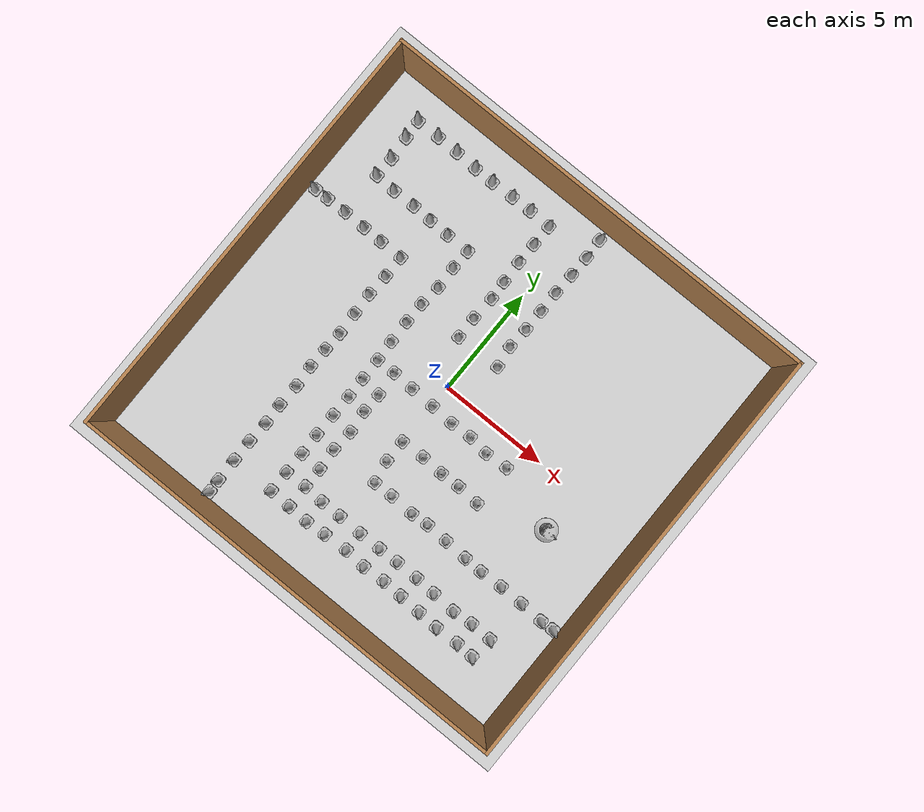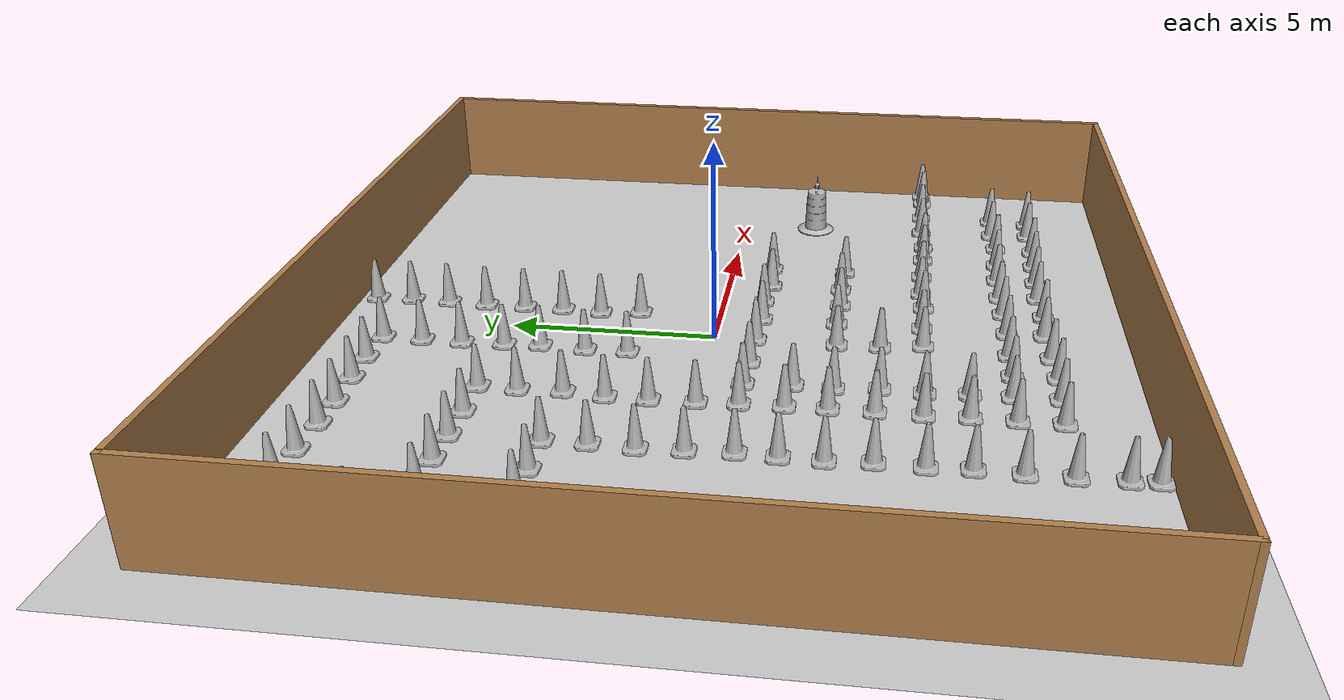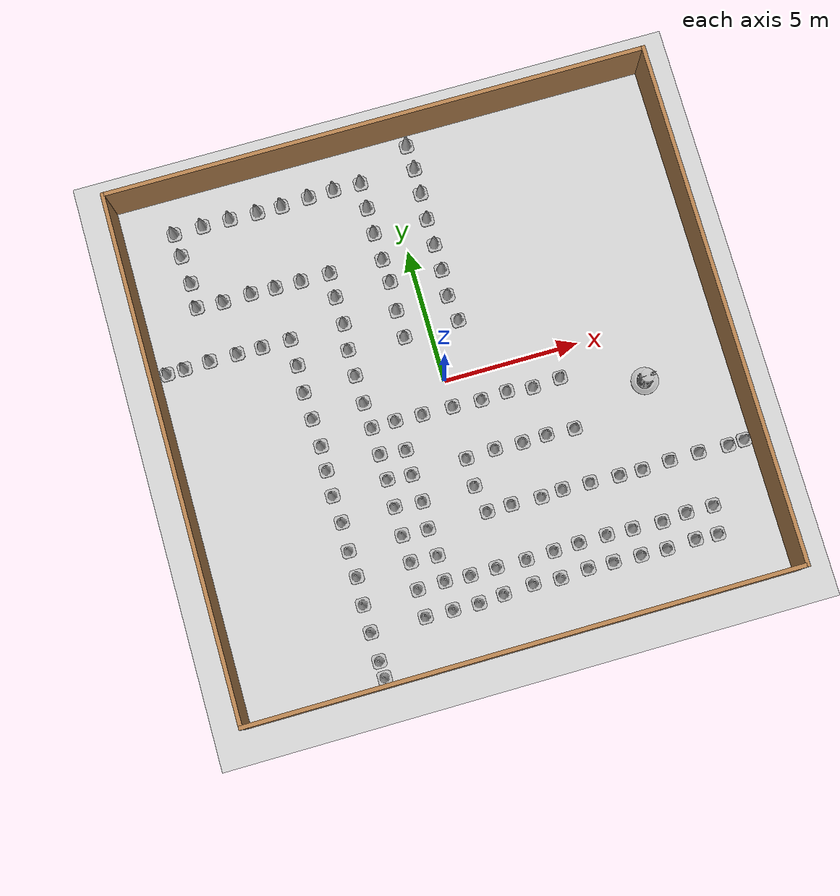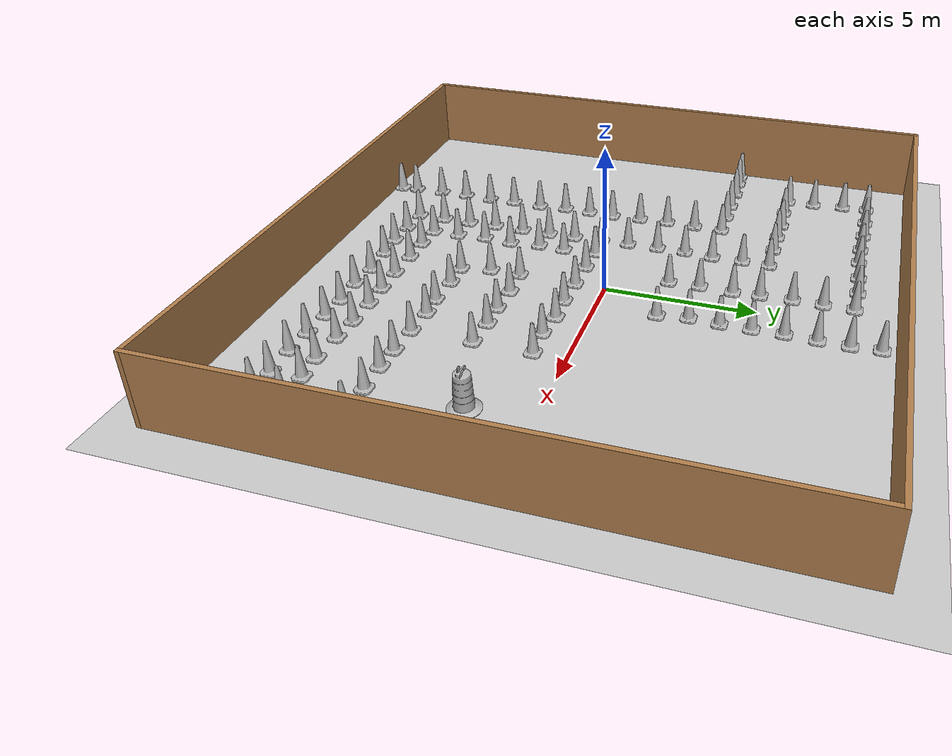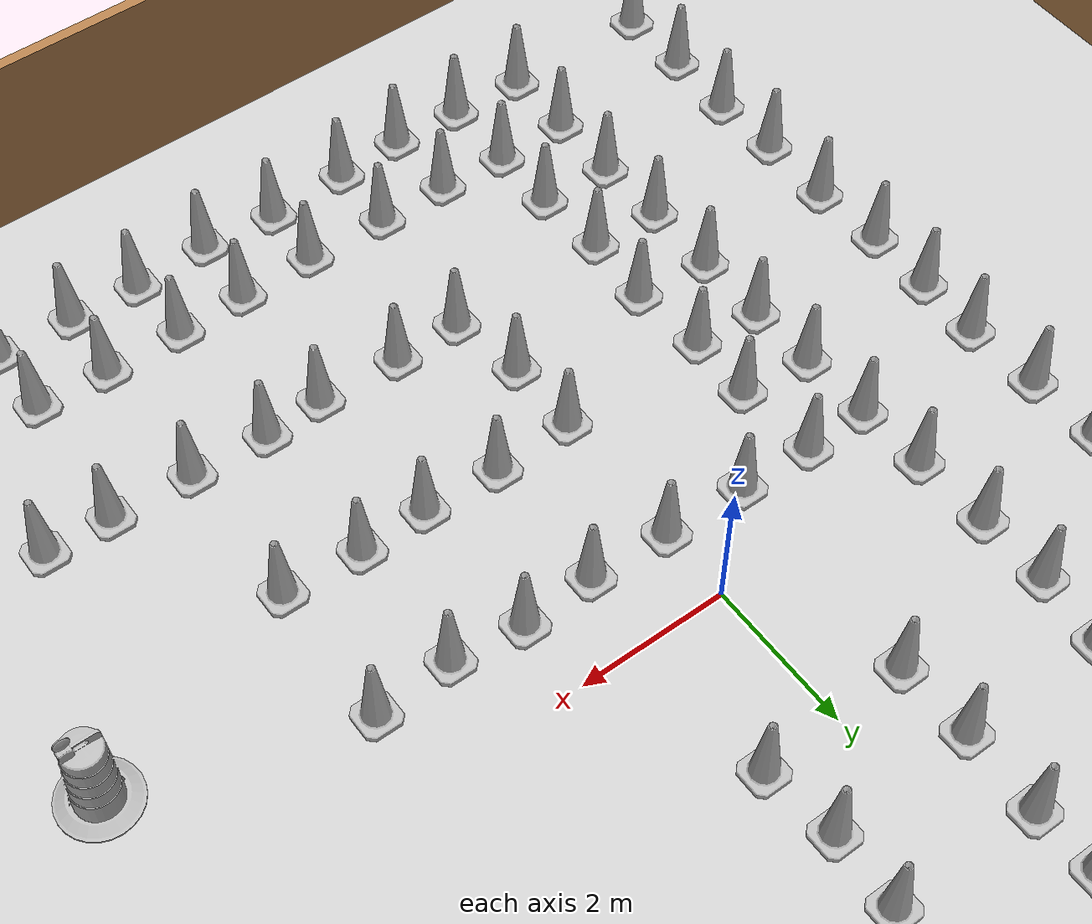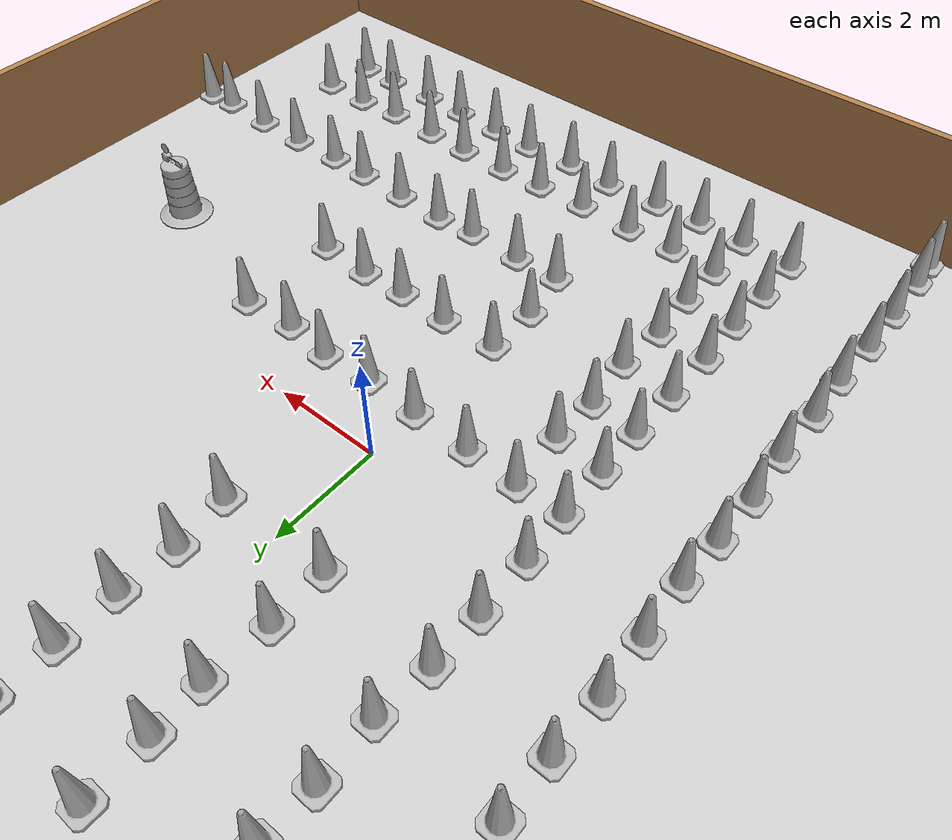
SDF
<sdf version="1.7">
 <world name="default">
  <light name="sun" type="directional">
   <pose>0 0 10 0 -0 0</pose>
   <diffuse>0.8 0.8 0.8 1</diffuse>
   <specular>0.2 0.2 0.2 1</specular>
   <attenuation>
    <range>1000</range>
    <constant>0.9</constant>
    <linear>0.01</linear>
    <quadratic>0.001</quadratic>
   </attenuation>
   <direction>-0.5 0.1 -0.9</direction>
   <spot><inner_angle>0</inner_angle><outer_angle>0</outer_angle><falloff>0</falloff></spot>
  </light>
  <model name="ground_plane">
   <static>1</static>
   <link name="link">
    <collision name="collision">
     <geometry><plane><normal>0 0 1</normal><size>100 100</size></plane></geometry>
     <surface>
      <contact><collide_bitmask>65535</collide_bitmask></contact>
      <friction><ode><mu>100</mu><mu2>50</mu2></ode></friction>
     </surface>
    </collision>
    <visual name="visual">
     <cast_shadows>0</cast_shadows>
     <geometry><plane><normal>0 0 1</normal><size>100 100</size></plane></geometry>
     <material>
      <script><uri>file://media/materials/scripts/gazebo.material</uri><name>Gazebo/Grey</name></script>
     </material>
    </visual>
   </link>
  </model>
  <gravity>0 0 -9.8</gravity>
  <magnetic_field>6e-06 2.3e-05 -4.2e-05</magnetic_field>
  <atmosphere type="adiabatic"/>
  <physics type="ode">
   <max_step_size>0.001</max_step_size>
   <real_time_factor>1</real_time_factor>
   <real_time_update_rate>1000</real_time_update_rate>
  </physics>
  <scene><ambient>0.4 0.4 0.4 1</ambient><background>0.7 0.7 0.7 1</background><shadows>1</shadows></scene>
  <audio><device>default</device></audio>
  <spherical_coordinates>
   <surface_model>EARTH_WGS84</surface_model>
   <latitude_deg>0</latitude_deg>
   <longitude_deg>0</longitude_deg>
   <elevation>0</elevation>
   <heading_deg>0</heading_deg>
  </spherical_coordinates>
  <model name="my_building">
   <pose>0.05098 -0.313636 0 0 -0 0</pose>
   <link name="Wall_24">
    <collision name="Wall_24_Collision">
     <geometry><box><size>19.5 0.15 2.5</size></box></geometry>
     <pose>0 0 1.25 0 -0 0</pose>
    </collision>
    <visual name="Wall_24_Visual">
     <pose>0 0 1.25 0 -0 0</pose>
     <geometry><box><size>19.5 0.15 2.5</size></box></geometry>
     <material>
      <script><uri>file://media/materials/scripts/gazebo.material</uri><name>Gazebo/Wood</name></script>
      <ambient>0 0 0 1</ambient>
     </material>
     <meta><layer>0</layer></meta>
    </visual>
    <pose>-10.05 -0 0 0 -0 1.5708</pose>
   </link>
   <link name="Wall_25">
    <collision name="Wall_25_Collision">
     <geometry><box><size>20.25 0.15 2.5</size></box></geometry>
     <pose>0 0 1.25 0 -0 0</pose>
    </collision>
    <visual name="Wall_25_Visual">
     <pose>0 0 1.25 0 -0 0</pose>
     <geometry><box><size>20.25 0.15 2.5</size></box></geometry>
     <material>
      <script><uri>file://media/materials/scripts/gazebo.material</uri><name>Gazebo/Wood</name></script>
      <ambient>1 1 1 1</ambient>
     </material>
     <meta><layer>0</layer></meta>
    </visual>
    <pose>-0 9.675 0 0 -0 0</pose>
   </link>
   <link name="Wall_26">
    <collision name="Wall_26_Collision">
     <geometry><box><size>19.5 0.15 2.5</size></box></geometry>
     <pose>0 0 1.25 0 -0 0</pose>
    </collision>
    <visual name="Wall_26_Visual">
     <pose>0 0 1.25 0 -0 0</pose>
     <geometry><box><size>19.5 0.15 2.5</size></box></geometry>
     <material>
      <script><uri>file://media/materials/scripts/gazebo.material</uri><name>Gazebo/Wood</name></script>
      <ambient>1 1 1 1</ambient>
     </material>
     <meta><layer>0</layer></meta>
    </visual>
    <pose>10.05 -0 0 0 -0 -1.5708</pose>
   </link>
   <link name="Wall_29">
    <collision name="Wall_29_Collision">
     <geometry><box><size>20.25 0.15 2.5</size></box></geometry>
     <pose>0 0 1.25 0 -0 0</pose>
    </collision>
    <visual name="Wall_29_Visual">
     <pose>0 0 1.25 0 -0 0</pose>
     <geometry><box><size>20.25 0.15 2.5</size></box></geometry>
     <material>
      <script><uri>file://media/materials/scripts/gazebo.material</uri><name>Gazebo/Wood</name></script>
      <ambient>1 1 1 1</ambient>
     </material>
     <meta><layer>0</layer></meta>
    </visual>
    <pose>-0 -9.675 0 0 -0 3.14159</pose>
   </link>
   <static>1</static>
  </model>
  <model name="Construction Cone">
   <link name="link">
    <collision name="collision">
     <geometry>
      <mesh><scale>10 10 10</scale><uri>model://construction_cone/meshes/construction_cone.dae</uri></mesh>
     </geometry>
    </collision>
    <visual name="visual">
     <geometry>
      <mesh><scale>10 10 10</scale><uri>model://construction_cone/meshes/construction_cone.dae</uri></mesh>
     </geometry>
    </visual>
    <inertial>
     <inertia><ixx>1</ixx><ixy>0</ixy><ixz>0</ixz><iyy>1</iyy><iyz>0</iyz><izz>1</izz></inertia>
     <mass>1</mass>
    </inertial>
   </link>
   <pose>-1.01799 5.99458 -6e-06 -4e-06 1e-06 0</pose>
  </model>
  <model name="Construction Cone_clone">
   <link name="link">
    <collision name="collision">
     <geometry>
      <mesh><scale>10 10 10</scale><uri>model://construction_cone/meshes/construction_cone.dae</uri></mesh>
     </geometry>
    </collision>
    <visual name="visual">
     <geometry>
      <mesh><scale>10 10 10</scale><uri>model://construction_cone/meshes/construction_cone.dae</uri></mesh>
     </geometry>
    </visual>
    <inertial>
     <inertia><ixx>1</ixx><ixy>0</ixy><ixz>0</ixz><iyy>1</iyy><iyz>0</iyz><izz>1</izz></inertia>
     <mass>1</mass>
    </inertial>
   </link>
   <pose>1.00618 4.98105 -0 0 -0 0</pose>
  </model>
  <model name="Construction Cone_clone_0">
   <link name="link">
    <collision name="collision">
     <geometry>
      <mesh><scale>10 10 10</scale><uri>model://construction_cone/meshes/construction_cone.dae</uri></mesh>
     </geometry>
    </collision>
    <visual name="visual">
     <geometry>
      <mesh><scale>10 10 10</scale><uri>model://construction_cone/meshes/construction_cone.dae</uri></mesh>
     </geometry>
    </visual>
    <inertial>
     <inertia><ixx>1</ixx><ixy>0</ixy><ixz>0</ixz><iyy>1</iyy><iyz>0</iyz><izz>1</izz></inertia>
     <mass>1</mass>
    </inertial>
   </link>
   <pose>1.00192 3.98917 1e-06 -3e-06 0 0</pose>
  </model>
  <model name="Construction Cone_clone_1">
   <link name="link">
    <collision name="collision">
     <geometry>
      <mesh><scale>10 10 10</scale><uri>model://construction_cone/meshes/construction_cone.dae</uri></mesh>
     </geometry>
    </collision>
    <visual name="visual">
     <geometry>
      <mesh><scale>10 10 10</scale><uri>model://construction_cone/meshes/construction_cone.dae</uri></mesh>
     </geometry>
    </visual>
    <inertial>
     <inertia><ixx>1</ixx><ixy>0</ixy><ixz>0</ixz><iyy>1</iyy><iyz>0</iyz><izz>1</izz></inertia>
     <mass>1</mass>
    </inertial>
   </link>
   <pose>-0.935036 4.0771 -6e-06 -4e-06 0 0</pose>
  </model>
  <model name="Construction Cone_clone_2">
   <link name="link">
    <collision name="collision">
     <geometry>
      <mesh><scale>10 10 10</scale><uri>model://construction_cone/meshes/construction_cone.dae</uri></mesh>
     </geometry>
    </collision>
    <visual name="visual">
     <geometry>
      <mesh><scale>10 10 10</scale><uri>model://construction_cone/meshes/construction_cone.dae</uri></mesh>
     </geometry>
    </visual>
    <inertial>
     <inertia><ixx>1</ixx><ixy>0</ixy><ixz>0</ixz><iyy>1</iyy><iyz>0</iyz><izz>1</izz></inertia>
     <mass>1</mass>
    </inertial>
   </link>
   <pose>1.07458 2.00845 0 -0 -0 -0</pose>
  </model>
  <model name="Construction Cone_clone_3">
   <link name="link">
    <collision name="collision">
     <geometry>
      <mesh><scale>10 10 10</scale><uri>model://construction_cone/meshes/construction_cone.dae</uri></mesh>
     </geometry>
    </collision>
    <visual name="visual">
     <geometry>
      <mesh><scale>10 10 10</scale><uri>model://construction_cone/meshes/construction_cone.dae</uri></mesh>
     </geometry>
    </visual>
    <inertial>
     <inertia><ixx>1</ixx><ixy>0</ixy><ixz>0</ixz><iyy>1</iyy><iyz>0</iyz><izz>1</izz></inertia>
     <mass>1</mass>
    </inertial>
   </link>
   <pose>-0.980101 1.94573 -0 0 -0 0</pose>
  </model>
  <model name="Construction Cone_clone_4">
   <link name="link">
    <collision name="collision">
     <geometry>
      <mesh><scale>10 10 10</scale><uri>model://construction_cone/meshes/construction_cone.dae</uri></mesh>
     </geometry>
    </collision>
    <visual name="visual">
     <geometry>
      <mesh><scale>10 10 10</scale><uri>model://construction_cone/meshes/construction_cone.dae</uri></mesh>
     </geometry>
    </visual>
    <inertial>
     <inertia><ixx>1</ixx><ixy>0</ixy><ixz>0</ixz><iyy>1</iyy><iyz>0</iyz><izz>1</izz></inertia>
     <mass>1</mass>
    </inertial>
   </link>
   <pose>-1.00552 6.97865 -0 1e-06 -0 0</pose>
  </model>
  <model name="Construction Cone_clone_5">
   <link name="link">
    <collision name="collision">
     <geometry>
      <mesh><scale>10 10 10</scale><uri>model://construction_cone/meshes/construction_cone.dae</uri></mesh>
     </geometry>
    </collision>
    <visual name="visual">
     <geometry>
      <mesh><scale>10 10 10</scale><uri>model://construction_cone/meshes/construction_cone.dae</uri></mesh>
     </geometry>
    </visual>
    <inertial>
     <inertia><ixx>1</ixx><ixy>0</ixy><ixz>0</ixz><iyy>1</iyy><iyz>0</iyz><izz>1</izz></inertia>
     <mass>1</mass>
    </inertial>
   </link>
   <pose>-0.990239 7.96121 0 -0 -0 -0</pose>
  </model>
  <model name="Construction Cone_clone_6">
   <link name="link">
    <collision name="collision">
     <geometry>
      <mesh><scale>10 10 10</scale><uri>model://construction_cone/meshes/construction_cone.dae</uri></mesh>
     </geometry>
    </collision>
    <visual name="visual">
     <geometry>
      <mesh><scale>10 10 10</scale><uri>model://construction_cone/meshes/construction_cone.dae</uri></mesh>
     </geometry>
    </visual>
    <inertial>
     <inertia><ixx>1</ixx><ixy>0</ixy><ixz>0</ixz><iyy>1</iyy><iyz>0</iyz><izz>1</izz></inertia>
     <mass>1</mass>
    </inertial>
   </link>
   <pose>1.02593 8.87266 -0 0 -1e-06 0</pose>
  </model>
  <model name="Construction Cone_clone_7">
   <link name="link">
    <collision name="collision">
     <geometry>
      <mesh><scale>10 10 10</scale><uri>model://construction_cone/meshes/construction_cone.dae</uri></mesh>
     </geometry>
    </collision>
    <visual name="visual">
     <geometry>
      <mesh><scale>10 10 10</scale><uri>model://construction_cone/meshes/construction_cone.dae</uri></mesh>
     </geometry>
    </visual>
    <inertial>
     <inertia><ixx>1</ixx><ixy>0</ixy><ixz>0</ixz><iyy>1</iyy><iyz>0</iyz><izz>1</izz></inertia>
     <mass>1</mass>
    </inertial>
   </link>
   <pose>-2.01651 7.99245 -0 0 -0 0</pose>
  </model>
  <model name="Construction Cone_clone_8">
   <link name="link">
    <collision name="collision">
     <geometry>
      <mesh><scale>10 10 10</scale><uri>model://construction_cone/meshes/construction_cone.dae</uri></mesh>
     </geometry>
    </collision>
    <visual name="visual">
     <geometry>
      <mesh><scale>10 10 10</scale><uri>model://construction_cone/meshes/construction_cone.dae</uri></mesh>
     </geometry>
    </visual>
    <inertial>
     <inertia><ixx>1</ixx><ixy>0</ixy><ixz>0</ixz><iyy>1</iyy><iyz>0</iyz><izz>1</izz></inertia>
     <mass>1</mass>
    </inertial>
   </link>
   <pose>-2.97184 7.96469 -8e-06 -6e-06 -0 -0</pose>
  </model>
  <model name="Construction Cone_clone_9">
   <link name="link">
    <collision name="collision">
     <geometry>
      <mesh><scale>10 10 10</scale><uri>model://construction_cone/meshes/construction_cone.dae</uri></mesh>
     </geometry>
    </collision>
    <visual name="visual">
     <geometry>
      <mesh><scale>10 10 10</scale><uri>model://construction_cone/meshes/construction_cone.dae</uri></mesh>
     </geometry>
    </visual>
    <inertial>
     <inertia><ixx>1</ixx><ixy>0</ixy><ixz>0</ixz><iyy>1</iyy><iyz>0</iyz><izz>1</izz></inertia>
     <mass>1</mass>
    </inertial>
   </link>
   <pose>1.06897 7.94604 -0 0 -0 0</pose>
  </model>
  <model name="Construction Cone_clone_10">
   <link name="link">
    <collision name="collision">
     <geometry>
      <mesh><scale>10 10 10</scale><uri>model://construction_cone/meshes/construction_cone.dae</uri></mesh>
     </geometry>
    </collision>
    <visual name="visual">
     <geometry>
      <mesh><scale>10 10 10</scale><uri>model://construction_cone/meshes/construction_cone.dae</uri></mesh>
     </geometry>
    </visual>
    <inertial>
     <inertia><ixx>1</ixx><ixy>0</ixy><ixz>0</ixz><iyy>1</iyy><iyz>0</iyz><izz>1</izz></inertia>
     <mass>1</mass>
    </inertial>
   </link>
   <pose>1.04507 6.98149 -0 0 -1e-06 0</pose>
  </model>
  <model name="Construction Cone_clone_11">
   <link name="link">
    <collision name="collision">
     <geometry>
      <mesh><scale>10 10 10</scale><uri>model://construction_cone/meshes/construction_cone.dae</uri></mesh>
     </geometry>
    </collision>
    <visual name="visual">
     <geometry>
      <mesh><scale>10 10 10</scale><uri>model://construction_cone/meshes/construction_cone.dae</uri></mesh>
     </geometry>
    </visual>
    <inertial>
     <inertia><ixx>1</ixx><ixy>0</ixy><ixz>0</ixz><iyy>1</iyy><iyz>0</iyz><izz>1</izz></inertia>
     <mass>1</mass>
    </inertial>
   </link>
   <pose>-0.986262 4.9569 -0 0 -0 0</pose>
  </model>
  <model name="Construction Cone_clone_12">
   <link name="link">
    <collision name="collision">
     <geometry>
      <mesh><scale>10 10 10</scale><uri>model://construction_cone/meshes/construction_cone.dae</uri></mesh>
     </geometry>
    </collision>
    <visual name="visual">
     <geometry>
      <mesh><scale>10 10 10</scale><uri>model://construction_cone/meshes/construction_cone.dae</uri></mesh>
     </geometry>
    </visual>
    <inertial>
     <inertia><ixx>1</ixx><ixy>0</ixy><ixz>0</ixz><iyy>1</iyy><iyz>0</iyz><izz>1</izz></inertia>
     <mass>1</mass>
    </inertial>
   </link>
   <pose>1.00019 5.97963 -9e-06 -1e-06 -0 -0</pose>
  </model>
  <model name="Construction Cone_clone_13">
   <link name="link">
    <collision name="collision">
     <geometry>
      <mesh><scale>10 10 10</scale><uri>model://construction_cone/meshes/construction_cone.dae</uri></mesh>
     </geometry>
    </collision>
    <visual name="visual">
     <geometry>
      <mesh><scale>10 10 10</scale><uri>model://construction_cone/meshes/construction_cone.dae</uri></mesh>
     </geometry>
    </visual>
    <inertial>
     <inertia><ixx>1</ixx><ixy>0</ixy><ixz>0</ixz><iyy>1</iyy><iyz>0</iyz><izz>1</izz></inertia>
     <mass>1</mass>
    </inertial>
   </link>
   <pose>-4.02289 7.91677 0 -0 -0 -0</pose>
  </model>
  <model name="Construction Cone_clone_14">
   <link name="link">
    <collision name="collision">
     <geometry>
      <mesh><scale>10 10 10</scale><uri>model://construction_cone/meshes/construction_cone.dae</uri></mesh>
     </geometry>
    </collision>
    <visual name="visual">
     <geometry>
      <mesh><scale>10 10 10</scale><uri>model://construction_cone/meshes/construction_cone.dae</uri></mesh>
     </geometry>
    </visual>
    <inertial>
     <inertia><ixx>1</ixx><ixy>0</ixy><ixz>0</ixz><iyy>1</iyy><iyz>0</iyz><izz>1</izz></inertia>
     <mass>1</mass>
    </inertial>
   </link>
   <pose>-4.94608 7.91863 -0 0 -0 0</pose>
  </model>
  <model name="Construction Cone_clone_15">
   <link name="link">
    <collision name="collision">
     <geometry>
      <mesh><scale>10 10 10</scale><uri>model://construction_cone/meshes/construction_cone.dae</uri></mesh>
     </geometry>
    </collision>
    <visual name="visual">
     <geometry>
      <mesh><scale>10 10 10</scale><uri>model://construction_cone/meshes/construction_cone.dae</uri></mesh>
     </geometry>
    </visual>
    <inertial>
     <inertia><ixx>1</ixx><ixy>0</ixy><ixz>0</ixz><iyy>1</iyy><iyz>0</iyz><izz>1</izz></inertia>
     <mass>1</mass>
    </inertial>
   </link>
   <pose>-5.97959 7.95857 -0 0 -0 0</pose>
  </model>
  <model name="Construction Cone_clone_16">
   <link name="link">
    <collision name="collision">
     <geometry>
      <mesh><scale>10 10 10</scale><uri>model://construction_cone/meshes/construction_cone.dae</uri></mesh>
     </geometry>
    </collision>
    <visual name="visual">
     <geometry>
      <mesh><scale>10 10 10</scale><uri>model://construction_cone/meshes/construction_cone.dae</uri></mesh>
     </geometry>
    </visual>
    <inertial>
     <inertia><ixx>1</ixx><ixy>0</ixy><ixz>0</ixz><iyy>1</iyy><iyz>0</iyz><izz>1</izz></inertia>
     <mass>1</mass>
    </inertial>
   </link>
   <pose>-7.01345 7.96661 -4e-06 4e-06 -1e-06 0</pose>
  </model>
  <model name="Construction Cone_clone_17">
   <link name="link">
    <collision name="collision">
     <geometry>
      <mesh><scale>10 10 10</scale><uri>model://construction_cone/meshes/construction_cone.dae</uri></mesh>
     </geometry>
    </collision>
    <visual name="visual">
     <geometry>
      <mesh><scale>10 10 10</scale><uri>model://construction_cone/meshes/construction_cone.dae</uri></mesh>
     </geometry>
    </visual>
    <inertial>
     <inertia><ixx>1</ixx><ixy>0</ixy><ixz>0</ixz><iyy>1</iyy><iyz>0</iyz><izz>1</izz></inertia>
     <mass>1</mass>
    </inertial>
   </link>
   <pose>-1.00066 2.97181 0 -0 -0 -0</pose>
  </model>
  <model name="Construction Cone_clone_18">
   <link name="link">
    <collision name="collision">
     <geometry>
      <mesh><scale>10 10 10</scale><uri>model://construction_cone/meshes/construction_cone.dae</uri></mesh>
     </geometry>
    </collision>
    <visual name="visual">
     <geometry>
      <mesh><scale>10 10 10</scale><uri>model://construction_cone/meshes/construction_cone.dae</uri></mesh>
     </geometry>
    </visual>
    <inertial>
     <inertia><ixx>1</ixx><ixy>0</ixy><ixz>0</ixz><iyy>1</iyy><iyz>0</iyz><izz>1</izz></inertia>
     <mass>1</mass>
    </inertial>
   </link>
   <pose>0.944633 3.00497 -6e-06 -4e-06 0 0</pose>
  </model>
  <model name="Construction Cone_clone_16_clone">
   <link name="link">
    <collision name="collision">
     <geometry>
      <mesh><scale>10 10 10</scale><uri>model://construction_cone/meshes/construction_cone.dae</uri></mesh>
     </geometry>
    </collision>
    <visual name="visual">
     <geometry>
      <mesh><scale>10 10 10</scale><uri>model://construction_cone/meshes/construction_cone.dae</uri></mesh>
     </geometry>
    </visual>
    <inertial>
     <inertia><ixx>1</ixx><ixy>0</ixy><ixz>0</ixz><iyy>1</iyy><iyz>0</iyz><izz>1</izz></inertia>
     <mass>1</mass>
    </inertial>
   </link>
   <pose>-8.10158 7.95749 0 -0 -0 -0</pose>
  </model>
  <model name="Construction Cone_clone_16_clone_0">
   <link name="link">
    <collision name="collision">
     <geometry>
      <mesh><scale>10 10 10</scale><uri>model://construction_cone/meshes/construction_cone.dae</uri></mesh>
     </geometry>
    </collision>
    <visual name="visual">
     <geometry>
      <mesh><scale>10 10 10</scale><uri>model://construction_cone/meshes/construction_cone.dae</uri></mesh>
     </geometry>
    </visual>
    <inertial>
     <inertia><ixx>1</ixx><ixy>0</ixy><ixz>0</ixz><iyy>1</iyy><iyz>0</iyz><izz>1</izz></inertia>
     <mass>1</mass>
    </inertial>
   </link>
   <pose>-8.05367 7.08406 -0 0 -0 0</pose>
  </model>
  <model name="Construction Cone_clone_16_clone_1">
   <link name="link">
    <collision name="collision">
     <geometry>
      <mesh><scale>10 10 10</scale><uri>model://construction_cone/meshes/construction_cone.dae</uri></mesh>
     </geometry>
    </collision>
    <visual name="visual">
     <geometry>
      <mesh><scale>10 10 10</scale><uri>model://construction_cone/meshes/construction_cone.dae</uri></mesh>
     </geometry>
    </visual>
    <inertial>
     <inertia><ixx>1</ixx><ixy>0</ixy><ixz>0</ixz><iyy>1</iyy><iyz>0</iyz><izz>1</izz></inertia>
     <mass>1</mass>
    </inertial>
   </link>
   <pose>-7.96652 6.00536 -0 0 -0 0</pose>
  </model>
  <model name="Construction Cone_clone_16_clone_2">
   <link name="link">
    <collision name="collision">
     <geometry>
      <mesh><scale>10 10 10</scale><uri>model://construction_cone/meshes/construction_cone.dae</uri></mesh>
     </geometry>
    </collision>
    <visual name="visual">
     <geometry>
      <mesh><scale>10 10 10</scale><uri>model://construction_cone/meshes/construction_cone.dae</uri></mesh>
     </geometry>
    </visual>
    <inertial>
     <inertia><ixx>1</ixx><ixy>0</ixy><ixz>0</ixz><iyy>1</iyy><iyz>0</iyz><izz>1</izz></inertia>
     <mass>1</mass>
    </inertial>
   </link>
   <pose>-7.98786 5.06189 -1e-06 2e-06 2e-06 0</pose>
  </model>
  <model name="Construction Cone_clone_16_clone_3">
   <link name="link">
    <collision name="collision">
     <geometry>
      <mesh><scale>10 10 10</scale><uri>model://construction_cone/meshes/construction_cone.dae</uri></mesh>
     </geometry>
    </collision>
    <visual name="visual">
     <geometry>
      <mesh><scale>10 10 10</scale><uri>model://construction_cone/meshes/construction_cone.dae</uri></mesh>
     </geometry>
    </visual>
    <inertial>
     <inertia><ixx>1</ixx><ixy>0</ixy><ixz>0</ixz><iyy>1</iyy><iyz>0</iyz><izz>1</izz></inertia>
     <mass>1</mass>
    </inertial>
   </link>
   <pose>-7.00541 5.00946 -0 0 -1e-06 0</pose>
  </model>
  <model name="Construction Cone_clone_16_clone_4">
   <link name="link">
    <collision name="collision">
     <geometry>
      <mesh><scale>10 10 10</scale><uri>model://construction_cone/meshes/construction_cone.dae</uri></mesh>
     </geometry>
    </collision>
    <visual name="visual">
     <geometry>
      <mesh><scale>10 10 10</scale><uri>model://construction_cone/meshes/construction_cone.dae</uri></mesh>
     </geometry>
    </visual>
    <inertial>
     <inertia><ixx>1</ixx><ixy>0</ixy><ixz>0</ixz><iyy>1</iyy><iyz>0</iyz><izz>1</izz></inertia>
     <mass>1</mass>
    </inertial>
   </link>
   <pose>-5.95433 5.0353 -0 0 -0 0</pose>
  </model>
  <model name="Construction Cone_clone_16_clone_5">
   <link name="link">
    <collision name="collision">
     <geometry>
      <mesh><scale>10 10 10</scale><uri>model://construction_cone/meshes/construction_cone.dae</uri></mesh>
     </geometry>
    </collision>
    <visual name="visual">
     <geometry>
      <mesh><scale>10 10 10</scale><uri>model://construction_cone/meshes/construction_cone.dae</uri></mesh>
     </geometry>
    </visual>
    <inertial>
     <inertia><ixx>1</ixx><ixy>0</ixy><ixz>0</ixz><iyy>1</iyy><iyz>0</iyz><izz>1</izz></inertia>
     <mass>1</mass>
    </inertial>
   </link>
   <pose>-5.03599 5.00389 -0 0 -0 0</pose>
  </model>
  <model name="Construction Cone_clone_16_clone_6">
   <link name="link">
    <collision name="collision">
     <geometry>
      <mesh><scale>10 10 10</scale><uri>model://construction_cone/meshes/construction_cone.dae</uri></mesh>
     </geometry>
    </collision>
    <visual name="visual">
     <geometry>
      <mesh><scale>10 10 10</scale><uri>model://construction_cone/meshes/construction_cone.dae</uri></mesh>
     </geometry>
    </visual>
    <inertial>
     <inertia><ixx>1</ixx><ixy>0</ixy><ixz>0</ixz><iyy>1</iyy><iyz>0</iyz><izz>1</izz></inertia>
     <mass>1</mass>
    </inertial>
   </link>
   <pose>-4.06945 4.98758 -0 0 -1e-06 0</pose>
  </model>
  <model name="Construction Cone_clone_16_clone_7">
   <link name="link">
    <collision name="collision">
     <geometry>
      <mesh><scale>10 10 10</scale><uri>model://construction_cone/meshes/construction_cone.dae</uri></mesh>
     </geometry>
    </collision>
    <visual name="visual">
     <geometry>
      <mesh><scale>10 10 10</scale><uri>model://construction_cone/meshes/construction_cone.dae</uri></mesh>
     </geometry>
    </visual>
    <inertial>
     <inertia><ixx>1</ixx><ixy>0</ixy><ixz>0</ixz><iyy>1</iyy><iyz>0</iyz><izz>1</izz></inertia>
     <mass>1</mass>
    </inertial>
   </link>
   <pose>-2.98074 4.99101 -5e-06 -4e-06 1e-06 0</pose>
  </model>
  <model name="Construction Cone_clone_16_clone_8">
   <link name="link">
    <collision name="collision">
     <geometry>
      <mesh><scale>10 10 10</scale><uri>model://construction_cone/meshes/construction_cone.dae</uri></mesh>
     </geometry>
    </collision>
    <visual name="visual">
     <geometry>
      <mesh><scale>10 10 10</scale><uri>model://construction_cone/meshes/construction_cone.dae</uri></mesh>
     </geometry>
    </visual>
    <inertial>
     <inertia><ixx>1</ixx><ixy>0</ixy><ixz>0</ixz><iyy>1</iyy><iyz>0</iyz><izz>1</izz></inertia>
     <mass>1</mass>
    </inertial>
   </link>
   <pose>-3.01413 4.06515 0 -0 -0 -0</pose>
  </model>
  <model name="Construction Cone_clone_16_clone_9">
   <link name="link">
    <collision name="collision">
     <geometry>
      <mesh><scale>10 10 10</scale><uri>model://construction_cone/meshes/construction_cone.dae</uri></mesh>
     </geometry>
    </collision>
    <visual name="visual">
     <geometry>
      <mesh><scale>10 10 10</scale><uri>model://construction_cone/meshes/construction_cone.dae</uri></mesh>
     </geometry>
    </visual>
    <inertial>
     <inertia><ixx>1</ixx><ixy>0</ixy><ixz>0</ixz><iyy>1</iyy><iyz>0</iyz><izz>1</izz></inertia>
     <mass>1</mass>
    </inertial>
   </link>
   <pose>-2.97922 3.02528 -0 0 -0 0</pose>
  </model>
  <model name="Construction Cone_clone_16_clone_10">
   <link name="link">
    <collision name="collision">
     <geometry>
      <mesh><scale>10 10 10</scale><uri>model://construction_cone/meshes/construction_cone.dae</uri></mesh>
     </geometry>
    </collision>
    <visual name="visual">
     <geometry>
      <mesh><scale>10 10 10</scale><uri>model://construction_cone/meshes/construction_cone.dae</uri></mesh>
     </geometry>
    </visual>
    <inertial>
     <inertia><ixx>1</ixx><ixy>0</ixy><ixz>0</ixz><iyy>1</iyy><iyz>0</iyz><izz>1</izz></inertia>
     <mass>1</mass>
    </inertial>
   </link>
   <pose>-3.08255 2.04324 -0 0 -0 0</pose>
  </model>
  <model name="Construction Cone_clone_16_clone_11">
   <link name="link">
    <collision name="collision">
     <geometry>
      <mesh><scale>10 10 10</scale><uri>model://construction_cone/meshes/construction_cone.dae</uri></mesh>
     </geometry>
    </collision>
    <visual name="visual">
     <geometry>
      <mesh><scale>10 10 10</scale><uri>model://construction_cone/meshes/construction_cone.dae</uri></mesh>
     </geometry>
    </visual>
    <inertial>
     <inertia><ixx>1</ixx><ixy>0</ixy><ixz>0</ixz><iyy>1</iyy><iyz>0</iyz><izz>1</izz></inertia>
     <mass>1</mass>
    </inertial>
   </link>
   <pose>-3.08639 1.06079 0 -0 -0 -0</pose>
  </model>
  <model name="Construction Cone_clone_16_clone_12">
   <link name="link">
    <collision name="collision">
     <geometry>
      <mesh><scale>10 10 10</scale><uri>model://construction_cone/meshes/construction_cone.dae</uri></mesh>
     </geometry>
    </collision>
    <visual name="visual">
     <geometry>
      <mesh><scale>10 10 10</scale><uri>model://construction_cone/meshes/construction_cone.dae</uri></mesh>
     </geometry>
    </visual>
    <inertial>
     <inertia><ixx>1</ixx><ixy>0</ixy><ixz>0</ixz><iyy>1</iyy><iyz>0</iyz><izz>1</izz></inertia>
     <mass>1</mass>
    </inertial>
   </link>
   <pose>-3.06053 0.003845 -0 0 -0 0</pose>
  </model>
  <model name="Construction Cone_clone_16_clone_13">
   <link name="link">
    <collision name="collision">
     <geometry>
      <mesh><scale>10 10 10</scale><uri>model://construction_cone/meshes/construction_cone.dae</uri></mesh>
     </geometry>
    </collision>
    <visual name="visual">
     <geometry>
      <mesh><scale>10 10 10</scale><uri>model://construction_cone/meshes/construction_cone.dae</uri></mesh>
     </geometry>
    </visual>
    <inertial>
     <inertia><ixx>1</ixx><ixy>0</ixy><ixz>0</ixz><iyy>1</iyy><iyz>0</iyz><izz>1</izz></inertia>
     <mass>1</mass>
    </inertial>
   </link>
   <pose>-3.01618 -0.949933 0 -0 -0 -0</pose>
  </model>
  <model name="Construction Cone_clone_16_clone_14">
   <link name="link">
    <collision name="collision">
     <geometry>
      <mesh><scale>10 10 10</scale><uri>model://construction_cone/meshes/construction_cone.dae</uri></mesh>
     </geometry>
    </collision>
    <visual name="visual">
     <geometry>
      <mesh><scale>10 10 10</scale><uri>model://construction_cone/meshes/construction_cone.dae</uri></mesh>
     </geometry>
    </visual>
    <inertial>
     <inertia><ixx>1</ixx><ixy>0</ixy><ixz>0</ixz><iyy>1</iyy><iyz>0</iyz><izz>1</izz></inertia>
     <mass>1</mass>
    </inertial>
   </link>
   <pose>-4.95464 -1.09419 -0 0 -1e-06 0</pose>
  </model>
  <model name="Construction Cone_clone_16_clone_15">
   <link name="link">
    <collision name="collision">
     <geometry>
      <mesh><scale>10 10 10</scale><uri>model://construction_cone/meshes/construction_cone.dae</uri></mesh>
     </geometry>
    </collision>
    <visual name="visual">
     <geometry>
      <mesh><scale>10 10 10</scale><uri>model://construction_cone/meshes/construction_cone.dae</uri></mesh>
     </geometry>
    </visual>
    <inertial>
     <inertia><ixx>1</ixx><ixy>0</ixy><ixz>0</ixz><iyy>1</iyy><iyz>0</iyz><izz>1</izz></inertia>
     <mass>1</mass>
    </inertial>
   </link>
   <pose>-5.00732 -0.05172 -1e-05 -0 -0 -0</pose>
  </model>
  <model name="Construction Cone_clone_16_clone_16">
   <link name="link">
    <collision name="collision">
     <geometry>
      <mesh><scale>10 10 10</scale><uri>model://construction_cone/meshes/construction_cone.dae</uri></mesh>
     </geometry>
    </collision>
    <visual name="visual">
     <geometry>
      <mesh><scale>10 10 10</scale><uri>model://construction_cone/meshes/construction_cone.dae</uri></mesh>
     </geometry>
    </visual>
    <inertial>
     <inertia><ixx>1</ixx><ixy>0</ixy><ixz>0</ixz><iyy>1</iyy><iyz>0</iyz><izz>1</izz></inertia>
     <mass>1</mass>
    </inertial>
   </link>
   <pose>-5.04654 0.972501 -1e-05 0 -0 0</pose>
  </model>
  <model name="Construction Cone_clone_16_clone_17">
   <link name="link">
    <collision name="collision">
     <geometry>
      <mesh><scale>10 10 10</scale><uri>model://construction_cone/meshes/construction_cone.dae</uri></mesh>
     </geometry>
    </collision>
    <visual name="visual">
     <geometry>
      <mesh><scale>10 10 10</scale><uri>model://construction_cone/meshes/construction_cone.dae</uri></mesh>
     </geometry>
    </visual>
    <inertial>
     <inertia><ixx>1</ixx><ixy>0</ixy><ixz>0</ixz><iyy>1</iyy><iyz>0</iyz><izz>1</izz></inertia>
     <mass>1</mass>
    </inertial>
   </link>
   <pose>-4.99937 1.99483 -0 0 -1e-06 0</pose>
  </model>
  <model name="Construction Cone_clone_16_clone_18">
   <link name="link">
    <collision name="collision">
     <geometry>
      <mesh><scale>10 10 10</scale><uri>model://construction_cone/meshes/construction_cone.dae</uri></mesh>
     </geometry>
    </collision>
    <visual name="visual">
     <geometry>
      <mesh><scale>10 10 10</scale><uri>model://construction_cone/meshes/construction_cone.dae</uri></mesh>
     </geometry>
    </visual>
    <inertial>
     <inertia><ixx>1</ixx><ixy>0</ixy><ixz>0</ixz><iyy>1</iyy><iyz>0</iyz><izz>1</izz></inertia>
     <mass>1</mass>
    </inertial>
   </link>
   <pose>-4.99962 2.99472 0 -0 -0 -0</pose>
  </model>
  <model name="Construction Cone_clone_16_clone_19">
   <link name="link">
    <collision name="collision">
     <geometry>
      <mesh><scale>10 10 10</scale><uri>model://construction_cone/meshes/construction_cone.dae</uri></mesh>
     </geometry>
    </collision>
    <visual name="visual">
     <geometry>
      <mesh><scale>10 10 10</scale><uri>model://construction_cone/meshes/construction_cone.dae</uri></mesh>
     </geometry>
    </visual>
    <inertial>
     <inertia><ixx>1</ixx><ixy>0</ixy><ixz>0</ixz><iyy>1</iyy><iyz>0</iyz><izz>1</izz></inertia>
     <mass>1</mass>
    </inertial>
   </link>
   <pose>-6.0715 2.99243 -0 0 -1e-06 0</pose>
  </model>
  <model name="Construction Cone_clone_16_clone_20">
   <link name="link">
    <collision name="collision">
     <geometry>
      <mesh><scale>10 10 10</scale><uri>model://construction_cone/meshes/construction_cone.dae</uri></mesh>
     </geometry>
    </collision>
    <visual name="visual">
     <geometry>
      <mesh><scale>10 10 10</scale><uri>model://construction_cone/meshes/construction_cone.dae</uri></mesh>
     </geometry>
    </visual>
    <inertial>
     <inertia><ixx>1</ixx><ixy>0</ixy><ixz>0</ixz><iyy>1</iyy><iyz>0</iyz><izz>1</izz></inertia>
     <mass>1</mass>
    </inertial>
   </link>
   <pose>-7 3 0 -0 -0 -0</pose>
  </model>
  <model name="Construction Cone_clone_16_clone_21">
   <link name="link">
    <collision name="collision">
     <geometry>
      <mesh><scale>10 10 10</scale><uri>model://construction_cone/meshes/construction_cone.dae</uri></mesh>
     </geometry>
    </collision>
    <visual name="visual">
     <geometry>
      <mesh><scale>10 10 10</scale><uri>model://construction_cone/meshes/construction_cone.dae</uri></mesh>
     </geometry>
    </visual>
    <inertial>
     <inertia><ixx>1</ixx><ixy>0</ixy><ixz>0</ixz><iyy>1</iyy><iyz>0</iyz><izz>1</izz></inertia>
     <mass>1</mass>
    </inertial>
   </link>
   <pose>-8.03271 3.01123 -0 0 -1e-06 0</pose>
  </model>
  <model name="Construction Cone_clone_16_clone_22">
   <link name="link">
    <collision name="collision">
     <geometry>
      <mesh><scale>10 10 10</scale><uri>model://construction_cone/meshes/construction_cone.dae</uri></mesh>
     </geometry>
    </collision>
    <visual name="visual">
     <geometry>
      <mesh><scale>10 10 10</scale><uri>model://construction_cone/meshes/construction_cone.dae</uri></mesh>
     </geometry>
    </visual>
    <inertial>
     <inertia><ixx>1</ixx><ixy>0</ixy><ixz>0</ixz><iyy>1</iyy><iyz>0</iyz><izz>1</izz></inertia>
     <mass>1</mass>
    </inertial>
   </link>
   <pose>-8.98005 2.97926 -0 0 -1e-06 0</pose>
  </model>
  <model name="Construction Cone_clone_16_clone_23">
   <link name="link">
    <collision name="collision">
     <geometry>
      <mesh><scale>10 10 10</scale><uri>model://construction_cone/meshes/construction_cone.dae</uri></mesh>
     </geometry>
    </collision>
    <visual name="visual">
     <geometry>
      <mesh><scale>10 10 10</scale><uri>model://construction_cone/meshes/construction_cone.dae</uri></mesh>
     </geometry>
    </visual>
    <inertial>
     <inertia><ixx>1</ixx><ixy>0</ixy><ixz>0</ixz><iyy>1</iyy><iyz>0</iyz><izz>1</izz></inertia>
     <mass>1</mass>
    </inertial>
   </link>
   <pose>-9.63265 2.96495 -0 0 -0 0</pose>
  </model>
  <model name="Construction Cone_clone_16_clone_24">
   <link name="link">
    <collision name="collision">
     <geometry>
      <mesh><scale>10 10 10</scale><uri>model://construction_cone/meshes/construction_cone.dae</uri></mesh>
     </geometry>
    </collision>
    <visual name="visual">
     <geometry>
      <mesh><scale>10 10 10</scale><uri>model://construction_cone/meshes/construction_cone.dae</uri></mesh>
     </geometry>
    </visual>
    <inertial>
     <inertia><ixx>1</ixx><ixy>0</ixy><ixz>0</ixz><iyy>1</iyy><iyz>0</iyz><izz>1</izz></inertia>
     <mass>1</mass>
    </inertial>
   </link>
   <pose>-5 -2 -0 0 -0 0</pose>
  </model>
  <model name="Construction Cone_clone_16_clone_25">
   <link name="link">
    <collision name="collision">
     <geometry>
      <mesh><scale>10 10 10</scale><uri>model://construction_cone/meshes/construction_cone.dae</uri></mesh>
     </geometry>
    </collision>
    <visual name="visual">
     <geometry>
      <mesh><scale>10 10 10</scale><uri>model://construction_cone/meshes/construction_cone.dae</uri></mesh>
     </geometry>
    </visual>
    <inertial>
     <inertia><ixx>1</ixx><ixy>0</ixy><ixz>0</ixz><iyy>1</iyy><iyz>0</iyz><izz>1</izz></inertia>
     <mass>1</mass>
    </inertial>
   </link>
   <pose>-2.9971 -1.95587 -0 -0 -0 -0</pose>
  </model>
  <model name="Construction Cone_clone_16_clone_26">
   <link name="link">
    <collision name="collision">
     <geometry>
      <mesh><scale>10 10 10</scale><uri>model://construction_cone/meshes/construction_cone.dae</uri></mesh>
     </geometry>
    </collision>
    <visual name="visual">
     <geometry>
      <mesh><scale>10 10 10</scale><uri>model://construction_cone/meshes/construction_cone.dae</uri></mesh>
     </geometry>
    </visual>
    <inertial>
     <inertia><ixx>1</ixx><ixy>0</ixy><ixz>0</ixz><iyy>1</iyy><iyz>0</iyz><izz>1</izz></inertia>
     <mass>1</mass>
    </inertial>
   </link>
   <pose>-2.9779 -2.90922 -1e-06 3e-06 -1e-06 0</pose>
  </model>
  <model name="Construction Cone_clone_16_clone_27">
   <link name="link">
    <collision name="collision">
     <geometry>
      <mesh><scale>10 10 10</scale><uri>model://construction_cone/meshes/construction_cone.dae</uri></mesh>
     </geometry>
    </collision>
    <visual name="visual">
     <geometry>
      <mesh><scale>10 10 10</scale><uri>model://construction_cone/meshes/construction_cone.dae</uri></mesh>
     </geometry>
    </visual>
    <inertial>
     <inertia><ixx>1</ixx><ixy>0</ixy><ixz>0</ixz><iyy>1</iyy><iyz>0</iyz><izz>1</izz></inertia>
     <mass>1</mass>
    </inertial>
   </link>
   <pose>-5.02675 -2.94747 -0 0 -0 0</pose>
  </model>
  <model name="Construction Cone_clone_16_clone_28">
   <link name="link">
    <collision name="collision">
     <geometry>
      <mesh><scale>10 10 10</scale><uri>model://construction_cone/meshes/construction_cone.dae</uri></mesh>
     </geometry>
    </collision>
    <visual name="visual">
     <geometry>
      <mesh><scale>10 10 10</scale><uri>model://construction_cone/meshes/construction_cone.dae</uri></mesh>
     </geometry>
    </visual>
    <inertial>
     <inertia><ixx>1</ixx><ixy>0</ixy><ixz>0</ixz><iyy>1</iyy><iyz>0</iyz><izz>1</izz></inertia>
     <mass>1</mass>
    </inertial>
   </link>
   <pose>-2.99086 -3.93175 -0 0 -1e-06 0</pose>
  </model>
  <model name="Construction Cone_clone_16_clone_29">
   <link name="link">
    <collision name="collision">
     <geometry>
      <mesh><scale>10 10 10</scale><uri>model://construction_cone/meshes/construction_cone.dae</uri></mesh>
     </geometry>
    </collision>
    <visual name="visual">
     <geometry>
      <mesh><scale>10 10 10</scale><uri>model://construction_cone/meshes/construction_cone.dae</uri></mesh>
     </geometry>
    </visual>
    <inertial>
     <inertia><ixx>1</ixx><ixy>0</ixy><ixz>0</ixz><iyy>1</iyy><iyz>0</iyz><izz>1</izz></inertia>
     <mass>1</mass>
    </inertial>
   </link>
   <pose>-4.96281 -3.9539 0 -0 -0 -0</pose>
  </model>
  <model name="Construction Cone_clone_16_clone_30">
   <link name="link">
    <collision name="collision">
     <geometry>
      <mesh><scale>10 10 10</scale><uri>model://construction_cone/meshes/construction_cone.dae</uri></mesh>
     </geometry>
    </collision>
    <visual name="visual">
     <geometry>
      <mesh><scale>10 10 10</scale><uri>model://construction_cone/meshes/construction_cone.dae</uri></mesh>
     </geometry>
    </visual>
    <inertial>
     <inertia><ixx>1</ixx><ixy>0</ixy><ixz>0</ixz><iyy>1</iyy><iyz>0</iyz><izz>1</izz></inertia>
     <mass>1</mass>
    </inertial>
   </link>
   <pose>-3.00531 -4.98866 -5e-06 -4e-06 1e-06 0</pose>
  </model>
  <model name="Construction Cone_clone_16_clone_31">
   <link name="link">
    <collision name="collision">
     <geometry>
      <mesh><scale>10 10 10</scale><uri>model://construction_cone/meshes/construction_cone.dae</uri></mesh>
     </geometry>
    </collision>
    <visual name="visual">
     <geometry>
      <mesh><scale>10 10 10</scale><uri>model://construction_cone/meshes/construction_cone.dae</uri></mesh>
     </geometry>
    </visual>
    <inertial>
     <inertia><ixx>1</ixx><ixy>0</ixy><ixz>0</ixz><iyy>1</iyy><iyz>0</iyz><izz>1</izz></inertia>
     <mass>1</mass>
    </inertial>
   </link>
   <pose>-4.9963 -5.0118 0 -0 -0 -0</pose>
  </model>
  <model name="Construction Cone_clone_16_clone_32">
   <link name="link">
    <collision name="collision">
     <geometry>
      <mesh><scale>10 10 10</scale><uri>model://construction_cone/meshes/construction_cone.dae</uri></mesh>
     </geometry>
    </collision>
    <visual name="visual">
     <geometry>
      <mesh><scale>10 10 10</scale><uri>model://construction_cone/meshes/construction_cone.dae</uri></mesh>
     </geometry>
    </visual>
    <inertial>
     <inertia><ixx>1</ixx><ixy>0</ixy><ixz>0</ixz><iyy>1</iyy><iyz>0</iyz><izz>1</izz></inertia>
     <mass>1</mass>
    </inertial>
   </link>
   <pose>-2.97008 -5.99304 -0 0 -0 0</pose>
  </model>
  <model name="Construction Cone_clone_16_clone_33">
   <link name="link">
    <collision name="collision">
     <geometry>
      <mesh><scale>10 10 10</scale><uri>model://construction_cone/meshes/construction_cone.dae</uri></mesh>
     </geometry>
    </collision>
    <visual name="visual">
     <geometry>
      <mesh><scale>10 10 10</scale><uri>model://construction_cone/meshes/construction_cone.dae</uri></mesh>
     </geometry>
    </visual>
    <inertial>
     <inertia><ixx>1</ixx><ixy>0</ixy><ixz>0</ixz><iyy>1</iyy><iyz>0</iyz><izz>1</izz></inertia>
     <mass>1</mass>
    </inertial>
   </link>
   <pose>-4.95897 -5.96865 -5e-06 -4e-06 1e-06 0</pose>
  </model>
  <model name="Construction Cone_clone_16_clone_34">
   <link name="link">
    <collision name="collision">
     <geometry>
      <mesh><scale>10 10 10</scale><uri>model://construction_cone/meshes/construction_cone.dae</uri></mesh>
     </geometry>
    </collision>
    <visual name="visual">
     <geometry>
      <mesh><scale>10 10 10</scale><uri>model://construction_cone/meshes/construction_cone.dae</uri></mesh>
     </geometry>
    </visual>
    <inertial>
     <inertia><ixx>1</ixx><ixy>0</ixy><ixz>0</ixz><iyy>1</iyy><iyz>0</iyz><izz>1</izz></inertia>
     <mass>1</mass>
    </inertial>
   </link>
   <pose>-2.98774 -7.00257 -0 0 -1e-06 0</pose>
  </model>
  <model name="Construction Cone_clone_16_clone_35">
   <link name="link">
    <collision name="collision">
     <geometry>
      <mesh><scale>10 10 10</scale><uri>model://construction_cone/meshes/construction_cone.dae</uri></mesh>
     </geometry>
    </collision>
    <visual name="visual">
     <geometry>
      <mesh><scale>10 10 10</scale><uri>model://construction_cone/meshes/construction_cone.dae</uri></mesh>
     </geometry>
    </visual>
    <inertial>
     <inertia><ixx>1</ixx><ixy>0</ixy><ixz>0</ixz><iyy>1</iyy><iyz>0</iyz><izz>1</izz></inertia>
     <mass>1</mass>
    </inertial>
   </link>
   <pose>-5.00679 -6.99197 -3e-06 -3e-06 -1e-06 -0</pose>
  </model>
  <model name="Construction Cone_clone_16_clone_36">
   <link name="link">
    <collision name="collision">
     <geometry>
      <mesh><scale>10 10 10</scale><uri>model://construction_cone/meshes/construction_cone.dae</uri></mesh>
     </geometry>
    </collision>
    <visual name="visual">
     <geometry>
      <mesh><scale>10 10 10</scale><uri>model://construction_cone/meshes/construction_cone.dae</uri></mesh>
     </geometry>
    </visual>
    <inertial>
     <inertia><ixx>1</ixx><ixy>0</ixy><ixz>0</ixz><iyy>1</iyy><iyz>0</iyz><izz>1</izz></inertia>
     <mass>1</mass>
    </inertial>
   </link>
   <pose>-2.98773 -8.00367 -8e-06 1e-06 -0 0</pose>
  </model>
  <model name="Construction Cone_clone_16_clone_37">
   <link name="link">
    <collision name="collision">
     <geometry>
      <mesh><scale>10 10 10</scale><uri>model://construction_cone/meshes/construction_cone.dae</uri></mesh>
     </geometry>
    </collision>
    <visual name="visual">
     <geometry>
      <mesh><scale>10 10 10</scale><uri>model://construction_cone/meshes/construction_cone.dae</uri></mesh>
     </geometry>
    </visual>
    <inertial>
     <inertia><ixx>1</ixx><ixy>0</ixy><ixz>0</ixz><iyy>1</iyy><iyz>0</iyz><izz>1</izz></inertia>
     <mass>1</mass>
    </inertial>
   </link>
   <pose>-5 -8 -8e-06 -5e-06 -0 -0</pose>
  </model>
  <model name="Construction Cone_clone_16_clone_38">
   <link name="link">
    <collision name="collision">
     <geometry>
      <mesh><scale>10 10 10</scale><uri>model://construction_cone/meshes/construction_cone.dae</uri></mesh>
     </geometry>
    </collision>
    <visual name="visual">
     <geometry>
      <mesh><scale>10 10 10</scale><uri>model://construction_cone/meshes/construction_cone.dae</uri></mesh>
     </geometry>
    </visual>
    <inertial>
     <inertia><ixx>1</ixx><ixy>0</ixy><ixz>0</ixz><iyy>1</iyy><iyz>0</iyz><izz>1</izz></inertia>
     <mass>1</mass>
    </inertial>
   </link>
   <pose>-1.02304 -8.05975 -9e-06 1e-06 -1e-06 0</pose>
  </model>
  <model name="Construction Cone_clone_16_clone_39">
   <link name="link">
    <collision name="collision">
     <geometry>
      <mesh><scale>10 10 10</scale><uri>model://construction_cone/meshes/construction_cone.dae</uri></mesh>
     </geometry>
    </collision>
    <visual name="visual">
     <geometry>
      <mesh><scale>10 10 10</scale><uri>model://construction_cone/meshes/construction_cone.dae</uri></mesh>
     </geometry>
    </visual>
    <inertial>
     <inertia><ixx>1</ixx><ixy>0</ixy><ixz>0</ixz><iyy>1</iyy><iyz>0</iyz><izz>1</izz></inertia>
     <mass>1</mass>
    </inertial>
   </link>
   <pose>-4.98064 -9.05839 -3e-06 -3e-06 -1e-06 -0</pose>
  </model>
  <model name="Construction Cone_clone_16_clone_40">
   <link name="link">
    <collision name="collision">
     <geometry>
      <mesh><scale>10 10 10</scale><uri>model://construction_cone/meshes/construction_cone.dae</uri></mesh>
     </geometry>
    </collision>
    <visual name="visual">
     <geometry>
      <mesh><scale>10 10 10</scale><uri>model://construction_cone/meshes/construction_cone.dae</uri></mesh>
     </geometry>
    </visual>
    <inertial>
     <inertia><ixx>1</ixx><ixy>0</ixy><ixz>0</ixz><iyy>1</iyy><iyz>0</iyz><izz>1</izz></inertia>
     <mass>1</mass>
    </inertial>
   </link>
   <pose>-4.95094 -9.66216 -0 0 0 -1.7e-05</pose>
  </model>
  <model name="Construction Cone_clone_16_clone_41">
   <link name="link">
    <collision name="collision">
     <geometry>
      <mesh><scale>10 10 10</scale><uri>model://construction_cone/meshes/construction_cone.dae</uri></mesh>
     </geometry>
    </collision>
    <visual name="visual">
     <geometry>
      <mesh><scale>10 10 10</scale><uri>model://construction_cone/meshes/construction_cone.dae</uri></mesh>
     </geometry>
    </visual>
    <inertial>
     <inertia><ixx>1</ixx><ixy>0</ixy><ixz>0</ixz><iyy>1</iyy><iyz>0</iyz><izz>1</izz></inertia>
     <mass>1</mass>
    </inertial>
   </link>
   <pose>-1.9826 -8.03378 -0 0 -1e-06 0</pose>
  </model>
  <model name="Construction Cone_clone_16_clone_42">
   <link name="link">
    <collision name="collision">
     <geometry>
      <mesh><scale>10 10 10</scale><uri>model://construction_cone/meshes/construction_cone.dae</uri></mesh>
     </geometry>
    </collision>
    <visual name="visual">
     <geometry>
      <mesh><scale>10 10 10</scale><uri>model://construction_cone/meshes/construction_cone.dae</uri></mesh>
     </geometry>
    </visual>
    <inertial>
     <inertia><ixx>1</ixx><ixy>0</ixy><ixz>0</ixz><iyy>1</iyy><iyz>0</iyz><izz>1</izz></inertia>
     <mass>1</mass>
    </inertial>
   </link>
   <pose>-0.093011 -7.99219 -0 0 -1e-06 0</pose>
  </model>
  <model name="Construction Cone_clone_16_clone_43">
   <link name="link">
    <collision name="collision">
     <geometry>
      <mesh><scale>10 10 10</scale><uri>model://construction_cone/meshes/construction_cone.dae</uri></mesh>
     </geometry>
    </collision>
    <visual name="visual">
     <geometry>
      <mesh><scale>10 10 10</scale><uri>model://construction_cone/meshes/construction_cone.dae</uri></mesh>
     </geometry>
    </visual>
    <inertial>
     <inertia><ixx>1</ixx><ixy>0</ixy><ixz>0</ixz><iyy>1</iyy><iyz>0</iyz><izz>1</izz></inertia>
     <mass>1</mass>
    </inertial>
   </link>
   <pose>1.01673 -7.92565 -6e-06 2e-06 -0 0</pose>
  </model>
  <model name="Construction Cone_clone_16_clone_44">
   <link name="link">
    <collision name="collision">
     <geometry>
      <mesh><scale>10 10 10</scale><uri>model://construction_cone/meshes/construction_cone.dae</uri></mesh>
     </geometry>
    </collision>
    <visual name="visual">
     <geometry>
      <mesh><scale>10 10 10</scale><uri>model://construction_cone/meshes/construction_cone.dae</uri></mesh>
     </geometry>
    </visual>
    <inertial>
     <inertia><ixx>1</ixx><ixy>0</ixy><ixz>0</ixz><iyy>1</iyy><iyz>0</iyz><izz>1</izz></inertia>
     <mass>1</mass>
    </inertial>
   </link>
   <pose>2.01359 -7.99723 -4e-06 4e-06 -1e-06 0</pose>
  </model>
  <model name="Construction Cone_clone_16_clone_45">
   <link name="link">
    <collision name="collision">
     <geometry>
      <mesh><scale>10 10 10</scale><uri>model://construction_cone/meshes/construction_cone.dae</uri></mesh>
     </geometry>
    </collision>
    <visual name="visual">
     <geometry>
      <mesh><scale>10 10 10</scale><uri>model://construction_cone/meshes/construction_cone.dae</uri></mesh>
     </geometry>
    </visual>
    <inertial>
     <inertia><ixx>1</ixx><ixy>0</ixy><ixz>0</ixz><iyy>1</iyy><iyz>0</iyz><izz>1</izz></inertia>
     <mass>1</mass>
    </inertial>
   </link>
   <pose>3.05139 -7.93503 -1e-05 -1e-06 0 0</pose>
  </model>
  <model name="Construction Cone_clone_16_clone_46">
   <link name="link">
    <collision name="collision">
     <geometry>
      <mesh><scale>10 10 10</scale><uri>model://construction_cone/meshes/construction_cone.dae</uri></mesh>
     </geometry>
    </collision>
    <visual name="visual">
     <geometry>
      <mesh><scale>10 10 10</scale><uri>model://construction_cone/meshes/construction_cone.dae</uri></mesh>
     </geometry>
    </visual>
    <inertial>
     <inertia><ixx>1</ixx><ixy>0</ixy><ixz>0</ixz><iyy>1</iyy><iyz>0</iyz><izz>1</izz></inertia>
     <mass>1</mass>
    </inertial>
   </link>
   <pose>3.98556 -7.96249 -6e-06 -4e-06 0 0</pose>
  </model>
  <model name="Construction Cone_clone_16_clone_47">
   <link name="link">
    <collision name="collision">
     <geometry>
      <mesh><scale>10 10 10</scale><uri>model://construction_cone/meshes/construction_cone.dae</uri></mesh>
     </geometry>
    </collision>
    <visual name="visual">
     <geometry>
      <mesh><scale>10 10 10</scale><uri>model://construction_cone/meshes/construction_cone.dae</uri></mesh>
     </geometry>
    </visual>
    <inertial>
     <inertia><ixx>1</ixx><ixy>0</ixy><ixz>0</ixz><iyy>1</iyy><iyz>0</iyz><izz>1</izz></inertia>
     <mass>1</mass>
    </inertial>
   </link>
   <pose>5.00339 -7.99684 -9e-06 -1e-06 -0 -0</pose>
  </model>
  <model name="Construction Cone_clone_16_clone_48">
   <link name="link">
    <collision name="collision">
     <geometry>
      <mesh><scale>10 10 10</scale><uri>model://construction_cone/meshes/construction_cone.dae</uri></mesh>
     </geometry>
    </collision>
    <visual name="visual">
     <geometry>
      <mesh><scale>10 10 10</scale><uri>model://construction_cone/meshes/construction_cone.dae</uri></mesh>
     </geometry>
    </visual>
    <inertial>
     <inertia><ixx>1</ixx><ixy>0</ixy><ixz>0</ixz><iyy>1</iyy><iyz>0</iyz><izz>1</izz></inertia>
     <mass>1</mass>
    </inertial>
   </link>
   <pose>5.96116 -8.03472 -0 0 -1e-06 0</pose>
  </model>
  <model name="Construction Cone_clone_16_clone_49">
   <link name="link">
    <collision name="collision">
     <geometry>
      <mesh><scale>10 10 10</scale><uri>model://construction_cone/meshes/construction_cone.dae</uri></mesh>
     </geometry>
    </collision>
    <visual name="visual">
     <geometry>
      <mesh><scale>10 10 10</scale><uri>model://construction_cone/meshes/construction_cone.dae</uri></mesh>
     </geometry>
    </visual>
    <inertial>
     <inertia><ixx>1</ixx><ixy>0</ixy><ixz>0</ixz><iyy>1</iyy><iyz>0</iyz><izz>1</izz></inertia>
     <mass>1</mass>
    </inertial>
   </link>
   <pose>7.03824 -7.98914 -0 0 -0 0</pose>
  </model>
  <model name="Construction Cone_clone_16_clone_50">
   <link name="link">
    <collision name="collision">
     <geometry>
      <mesh><scale>10 10 10</scale><uri>model://construction_cone/meshes/construction_cone.dae</uri></mesh>
     </geometry>
    </collision>
    <visual name="visual">
     <geometry>
      <mesh><scale>10 10 10</scale><uri>model://construction_cone/meshes/construction_cone.dae</uri></mesh>
     </geometry>
    </visual>
    <inertial>
     <inertia><ixx>1</ixx><ixy>0</ixy><ixz>0</ixz><iyy>1</iyy><iyz>0</iyz><izz>1</izz></inertia>
     <mass>1</mass>
    </inertial>
   </link>
   <pose>7.86495 -8.02301 -0 0 -0 0</pose>
  </model>
  <model name="Construction Cone_clone_16_clone_51">
   <link name="link">
    <collision name="collision">
     <geometry>
      <mesh><scale>10 10 10</scale><uri>model://construction_cone/meshes/construction_cone.dae</uri></mesh>
     </geometry>
    </collision>
    <visual name="visual">
     <geometry>
      <mesh><scale>10 10 10</scale><uri>model://construction_cone/meshes/construction_cone.dae</uri></mesh>
     </geometry>
    </visual>
    <inertial>
     <inertia><ixx>1</ixx><ixy>0</ixy><ixz>0</ixz><iyy>1</iyy><iyz>0</iyz><izz>1</izz></inertia>
     <mass>1</mass>
    </inertial>
   </link>
   <pose>8 -7 -1e-05 -1e-06 0 0</pose>
  </model>
  <model name="Construction Cone_clone_16_clone_52">
   <link name="link">
    <collision name="collision">
     <geometry>
      <mesh><scale>10 10 10</scale><uri>model://construction_cone/meshes/construction_cone.dae</uri></mesh>
     </geometry>
    </collision>
    <visual name="visual">
     <geometry>
      <mesh><scale>10 10 10</scale><uri>model://construction_cone/meshes/construction_cone.dae</uri></mesh>
     </geometry>
    </visual>
    <inertial>
     <inertia><ixx>1</ixx><ixy>0</ixy><ixz>0</ixz><iyy>1</iyy><iyz>0</iyz><izz>1</izz></inertia>
     <mass>1</mass>
    </inertial>
   </link>
   <pose>9.77379 -5.03681 -0 0 -0 0.004282</pose>
  </model>
  <model name="Construction Cone_clone_16_clone_53">
   <link name="link">
    <collision name="collision">
     <geometry>
      <mesh><scale>10 10 10</scale><uri>model://construction_cone/meshes/construction_cone.dae</uri></mesh>
     </geometry>
    </collision>
    <visual name="visual">
     <geometry>
      <mesh><scale>10 10 10</scale><uri>model://construction_cone/meshes/construction_cone.dae</uri></mesh>
     </geometry>
    </visual>
    <inertial>
     <inertia><ixx>1</ixx><ixy>0</ixy><ixz>0</ixz><iyy>1</iyy><iyz>0</iyz><izz>1</izz></inertia>
     <mass>1</mass>
    </inertial>
   </link>
   <pose>9.16677 -5.06825 -8e-06 0 1e-06 0</pose>
  </model>
  <model name="Construction Cone_clone_16_clone_54">
   <link name="link">
    <collision name="collision">
     <geometry>
      <mesh><scale>10 10 10</scale><uri>model://construction_cone/meshes/construction_cone.dae</uri></mesh>
     </geometry>
    </collision>
    <visual name="visual">
     <geometry>
      <mesh><scale>10 10 10</scale><uri>model://construction_cone/meshes/construction_cone.dae</uri></mesh>
     </geometry>
    </visual>
    <inertial>
     <inertia><ixx>1</ixx><ixy>0</ixy><ixz>0</ixz><iyy>1</iyy><iyz>0</iyz><izz>1</izz></inertia>
     <mass>1</mass>
    </inertial>
   </link>
   <pose>8.06837 -5.02551 -0 0 -1e-06 0</pose>
  </model>
  <model name="Construction Cone_clone_16_clone_55">
   <link name="link">
    <collision name="collision">
     <geometry>
      <mesh><scale>10 10 10</scale><uri>model://construction_cone/meshes/construction_cone.dae</uri></mesh>
     </geometry>
    </collision>
    <visual name="visual">
     <geometry>
      <mesh><scale>10 10 10</scale><uri>model://construction_cone/meshes/construction_cone.dae</uri></mesh>
     </geometry>
    </visual>
    <inertial>
     <inertia><ixx>1</ixx><ixy>0</ixy><ixz>0</ixz><iyy>1</iyy><iyz>0</iyz><izz>1</izz></inertia>
     <mass>1</mass>
    </inertial>
   </link>
   <pose>6.98357 -5.01819 -0 0 -0 0</pose>
  </model>
  <model name="Construction Cone_clone_16_clone_56">
   <link name="link">
    <collision name="collision">
     <geometry>
      <mesh><scale>10 10 10</scale><uri>model://construction_cone/meshes/construction_cone.dae</uri></mesh>
     </geometry>
    </collision>
    <visual name="visual">
     <geometry>
      <mesh><scale>10 10 10</scale><uri>model://construction_cone/meshes/construction_cone.dae</uri></mesh>
     </geometry>
    </visual>
    <inertial>
     <inertia><ixx>1</ixx><ixy>0</ixy><ixz>0</ixz><iyy>1</iyy><iyz>0</iyz><izz>1</izz></inertia>
     <mass>1</mass>
    </inertial>
   </link>
   <pose>5.93798 -5.0688 -0 0 -1e-06 0</pose>
  </model>
  <model name="Construction Cone_clone_16_clone_57">
   <link name="link">
    <collision name="collision">
     <geometry>
      <mesh><scale>10 10 10</scale><uri>model://construction_cone/meshes/construction_cone.dae</uri></mesh>
     </geometry>
    </collision>
    <visual name="visual">
     <geometry>
      <mesh><scale>10 10 10</scale><uri>model://construction_cone/meshes/construction_cone.dae</uri></mesh>
     </geometry>
    </visual>
    <inertial>
     <inertia><ixx>1</ixx><ixy>0</ixy><ixz>0</ixz><iyy>1</iyy><iyz>0</iyz><izz>1</izz></inertia>
     <mass>1</mass>
    </inertial>
   </link>
   <pose>5.08082 -5.04785 -0 0 -0 0</pose>
  </model>
  <model name="Construction Cone_clone_16_clone_58">
   <link name="link">
    <collision name="collision">
     <geometry>
      <mesh><scale>10 10 10</scale><uri>model://construction_cone/meshes/construction_cone.dae</uri></mesh>
     </geometry>
    </collision>
    <visual name="visual">
     <geometry>
      <mesh><scale>10 10 10</scale><uri>model://construction_cone/meshes/construction_cone.dae</uri></mesh>
     </geometry>
    </visual>
    <inertial>
     <inertia><ixx>1</ixx><ixy>0</ixy><ixz>0</ixz><iyy>1</iyy><iyz>0</iyz><izz>1</izz></inertia>
     <mass>1</mass>
    </inertial>
   </link>
   <pose>4.00473 -5.00384 0 -0 -0 -0</pose>
  </model>
  <model name="Construction Cone_clone_16_clone_59">
   <link name="link">
    <collision name="collision">
     <geometry>
      <mesh><scale>10 10 10</scale><uri>model://construction_cone/meshes/construction_cone.dae</uri></mesh>
     </geometry>
    </collision>
    <visual name="visual">
     <geometry>
      <mesh><scale>10 10 10</scale><uri>model://construction_cone/meshes/construction_cone.dae</uri></mesh>
     </geometry>
    </visual>
    <inertial>
     <inertia><ixx>1</ixx><ixy>0</ixy><ixz>0</ixz><iyy>1</iyy><iyz>0</iyz><izz>1</izz></inertia>
     <mass>1</mass>
    </inertial>
   </link>
   <pose>2.977 -4.96881 -0 0 -0 0</pose>
  </model>
  <model name="Construction Cone_clone_16_clone_60">
   <link name="link">
    <collision name="collision">
     <geometry>
      <mesh><scale>10 10 10</scale><uri>model://construction_cone/meshes/construction_cone.dae</uri></mesh>
     </geometry>
    </collision>
    <visual name="visual">
     <geometry>
      <mesh><scale>10 10 10</scale><uri>model://construction_cone/meshes/construction_cone.dae</uri></mesh>
     </geometry>
    </visual>
    <inertial>
     <inertia><ixx>1</ixx><ixy>0</ixy><ixz>0</ixz><iyy>1</iyy><iyz>0</iyz><izz>1</izz></inertia>
     <mass>1</mass>
    </inertial>
   </link>
   <pose>2.17262 -5.02908 -9e-06 0 -0 0</pose>
  </model>
  <model name="Construction Cone_clone_16_clone_61">
   <link name="link">
    <collision name="collision">
     <geometry>
      <mesh><scale>10 10 10</scale><uri>model://construction_cone/meshes/construction_cone.dae</uri></mesh>
     </geometry>
    </collision>
    <visual name="visual">
     <geometry>
      <mesh><scale>10 10 10</scale><uri>model://construction_cone/meshes/construction_cone.dae</uri></mesh>
     </geometry>
    </visual>
    <inertial>
     <inertia><ixx>1</ixx><ixy>0</ixy><ixz>0</ixz><iyy>1</iyy><iyz>0</iyz><izz>1</izz></inertia>
     <mass>1</mass>
    </inertial>
   </link>
   <pose>1.05909 -4.98706 -0 0 -1e-06 0</pose>
  </model>
  <model name="Construction Cone_clone_16_clone_62">
   <link name="link">
    <collision name="collision">
     <geometry>
      <mesh><scale>10 10 10</scale><uri>model://construction_cone/meshes/construction_cone.dae</uri></mesh>
     </geometry>
    </collision>
    <visual name="visual">
     <geometry>
      <mesh><scale>10 10 10</scale><uri>model://construction_cone/meshes/construction_cone.dae</uri></mesh>
     </geometry>
    </visual>
    <inertial>
     <inertia><ixx>1</ixx><ixy>0</ixy><ixz>0</ixz><iyy>1</iyy><iyz>0</iyz><izz>1</izz></inertia>
     <mass>1</mass>
    </inertial>
   </link>
   <pose>0.154939 -5.00513 -0 0 -0 0</pose>
  </model>
  <model name="Construction Cone_clone_16_clone_63">
   <link name="link">
    <collision name="collision">
     <geometry>
      <mesh><scale>10 10 10</scale><uri>model://construction_cone/meshes/construction_cone.dae</uri></mesh>
     </geometry>
    </collision>
    <visual name="visual">
     <geometry>
      <mesh><scale>10 10 10</scale><uri>model://construction_cone/meshes/construction_cone.dae</uri></mesh>
     </geometry>
    </visual>
    <inertial>
     <inertia><ixx>1</ixx><ixy>0</ixy><ixz>0</ixz><iyy>1</iyy><iyz>0</iyz><izz>1</izz></inertia>
     <mass>1</mass>
    </inertial>
   </link>
   <pose>6.99932 -6.98303 0 -0 -0 -0</pose>
  </model>
  <model name="Construction Cone_clone_16_clone_64">
   <link name="link">
    <collision name="collision">
     <geometry>
      <mesh><scale>10 10 10</scale><uri>model://construction_cone/meshes/construction_cone.dae</uri></mesh>
     </geometry>
    </collision>
    <visual name="visual">
     <geometry>
      <mesh><scale>10 10 10</scale><uri>model://construction_cone/meshes/construction_cone.dae</uri></mesh>
     </geometry>
    </visual>
    <inertial>
     <inertia><ixx>1</ixx><ixy>0</ixy><ixz>0</ixz><iyy>1</iyy><iyz>0</iyz><izz>1</izz></inertia>
     <mass>1</mass>
    </inertial>
   </link>
   <pose>6.08052 -7.0619 -2e-06 -3e-06 -1e-06 -0</pose>
  </model>
  <model name="Construction Cone_clone_16_clone_65">
   <link name="link">
    <collision name="collision">
     <geometry>
      <mesh><scale>10 10 10</scale><uri>model://construction_cone/meshes/construction_cone.dae</uri></mesh>
     </geometry>
    </collision>
    <visual name="visual">
     <geometry>
      <mesh><scale>10 10 10</scale><uri>model://construction_cone/meshes/construction_cone.dae</uri></mesh>
     </geometry>
    </visual>
    <inertial>
     <inertia><ixx>1</ixx><ixy>0</ixy><ixz>0</ixz><iyy>1</iyy><iyz>0</iyz><izz>1</izz></inertia>
     <mass>1</mass>
    </inertial>
   </link>
   <pose>4.98571 -7.00816 -0 0 -0 0</pose>
  </model>
  <model name="Construction Cone_clone_16_clone_66">
   <link name="link">
    <collision name="collision">
     <geometry>
      <mesh><scale>10 10 10</scale><uri>model://construction_cone/meshes/construction_cone.dae</uri></mesh>
     </geometry>
    </collision>
    <visual name="visual">
     <geometry>
      <mesh><scale>10 10 10</scale><uri>model://construction_cone/meshes/construction_cone.dae</uri></mesh>
     </geometry>
    </visual>
    <inertial>
     <inertia><ixx>1</ixx><ixy>0</ixy><ixz>0</ixz><iyy>1</iyy><iyz>0</iyz><izz>1</izz></inertia>
     <mass>1</mass>
    </inertial>
   </link>
   <pose>4.03525 -6.96964 -9e-06 -1e-06 -0 -0</pose>
  </model>
  <model name="Construction Cone_clone_16_clone_67">
   <link name="link">
    <collision name="collision">
     <geometry>
      <mesh><scale>10 10 10</scale><uri>model://construction_cone/meshes/construction_cone.dae</uri></mesh>
     </geometry>
    </collision>
    <visual name="visual">
     <geometry>
      <mesh><scale>10 10 10</scale><uri>model://construction_cone/meshes/construction_cone.dae</uri></mesh>
     </geometry>
    </visual>
    <inertial>
     <inertia><ixx>1</ixx><ixy>0</ixy><ixz>0</ixz><iyy>1</iyy><iyz>0</iyz><izz>1</izz></inertia>
     <mass>1</mass>
    </inertial>
   </link>
   <pose>2.99112 -6.97246 -2e-06 -3e-06 -1e-06 -0</pose>
  </model>
  <model name="Construction Cone_clone_16_clone_68">
   <link name="link">
    <collision name="collision">
     <geometry>
      <mesh><scale>10 10 10</scale><uri>model://construction_cone/meshes/construction_cone.dae</uri></mesh>
     </geometry>
    </collision>
    <visual name="visual">
     <geometry>
      <mesh><scale>10 10 10</scale><uri>model://construction_cone/meshes/construction_cone.dae</uri></mesh>
     </geometry>
    </visual>
    <inertial>
     <inertia><ixx>1</ixx><ixy>0</ixy><ixz>0</ixz><iyy>1</iyy><iyz>0</iyz><izz>1</izz></inertia>
     <mass>1</mass>
    </inertial>
   </link>
   <pose>2.05653 -7.00448 -0 0 -0 0</pose>
  </model>
  <model name="Construction Cone_clone_16_clone_69">
   <link name="link">
    <collision name="collision">
     <geometry>
      <mesh><scale>10 10 10</scale><uri>model://construction_cone/meshes/construction_cone.dae</uri></mesh>
     </geometry>
    </collision>
    <visual name="visual">
     <geometry>
      <mesh><scale>10 10 10</scale><uri>model://construction_cone/meshes/construction_cone.dae</uri></mesh>
     </geometry>
    </visual>
    <inertial>
     <inertia><ixx>1</ixx><ixy>0</ixy><ixz>0</ixz><iyy>1</iyy><iyz>0</iyz><izz>1</izz></inertia>
     <mass>1</mass>
    </inertial>
   </link>
   <pose>1.0255 -7.03043 -6e-06 -4e-06 0 0</pose>
  </model>
  <model name="Construction Cone_clone_16_clone_70">
   <link name="link">
    <collision name="collision">
     <geometry>
      <mesh><scale>10 10 10</scale><uri>model://construction_cone/meshes/construction_cone.dae</uri></mesh>
     </geometry>
    </collision>
    <visual name="visual">
     <geometry>
      <mesh><scale>10 10 10</scale><uri>model://construction_cone/meshes/construction_cone.dae</uri></mesh>
     </geometry>
    </visual>
    <inertial>
     <inertia><ixx>1</ixx><ixy>0</ixy><ixz>0</ixz><iyy>1</iyy><iyz>0</iyz><izz>1</izz></inertia>
     <mass>1</mass>
    </inertial>
   </link>
   <pose>-0.081115 -7.01299 -0 0 -1e-06 0</pose>
  </model>
  <model name="Construction Cone_clone_16_clone_71">
   <link name="link">
    <collision name="collision">
     <geometry>
      <mesh><scale>10 10 10</scale><uri>model://construction_cone/meshes/construction_cone.dae</uri></mesh>
     </geometry>
    </collision>
    <visual name="visual">
     <geometry>
      <mesh><scale>10 10 10</scale><uri>model://construction_cone/meshes/construction_cone.dae</uri></mesh>
     </geometry>
    </visual>
    <inertial>
     <inertia><ixx>1</ixx><ixy>0</ixy><ixz>0</ixz><iyy>1</iyy><iyz>0</iyz><izz>1</izz></inertia>
     <mass>1</mass>
    </inertial>
   </link>
   <pose>-1.05377 -7.0235 -6e-06 -4e-06 0 0</pose>
  </model>
  <model name="Construction Cone_clone_16_clone_72">
   <link name="link">
    <collision name="collision">
     <geometry>
      <mesh><scale>10 10 10</scale><uri>model://construction_cone/meshes/construction_cone.dae</uri></mesh>
     </geometry>
    </collision>
    <visual name="visual">
     <geometry>
      <mesh><scale>10 10 10</scale><uri>model://construction_cone/meshes/construction_cone.dae</uri></mesh>
     </geometry>
    </visual>
    <inertial>
     <inertia><ixx>1</ixx><ixy>0</ixy><ixz>0</ixz><iyy>1</iyy><iyz>0</iyz><izz>1</izz></inertia>
     <mass>1</mass>
    </inertial>
   </link>
   <pose>-1.98356 -6.97147 -0 0 -0 0</pose>
  </model>
  <model name="Construction Cone_clone_16_clone_73">
   <link name="link">
    <collision name="collision">
     <geometry>
      <mesh><scale>10 10 10</scale><uri>model://construction_cone/meshes/construction_cone.dae</uri></mesh>
     </geometry>
    </collision>
    <visual name="visual">
     <geometry>
      <mesh><scale>10 10 10</scale><uri>model://construction_cone/meshes/construction_cone.dae</uri></mesh>
     </geometry>
    </visual>
    <inertial>
     <inertia><ixx>1</ixx><ixy>0</ixy><ixz>0</ixz><iyy>1</iyy><iyz>0</iyz><izz>1</izz></inertia>
     <mass>1</mass>
    </inertial>
   </link>
   <pose>-1.98693 -6.02465 -4e-06 4e-06 -1e-06 0</pose>
  </model>
  <model name="Construction Cone_clone_16_clone_74">
   <link name="link">
    <collision name="collision">
     <geometry>
      <mesh><scale>10 10 10</scale><uri>model://construction_cone/meshes/construction_cone.dae</uri></mesh>
     </geometry>
    </collision>
    <visual name="visual">
     <geometry>
      <mesh><scale>10 10 10</scale><uri>model://construction_cone/meshes/construction_cone.dae</uri></mesh>
     </geometry>
    </visual>
    <inertial>
     <inertia><ixx>1</ixx><ixy>0</ixy><ixz>0</ixz><iyy>1</iyy><iyz>0</iyz><izz>1</izz></inertia>
     <mass>1</mass>
    </inertial>
   </link>
   <pose>-2.05517 -5.01669 -1e-05 0 -0 0</pose>
  </model>
  <model name="Construction Cone_clone_16_clone_75">
   <link name="link">
    <collision name="collision">
     <geometry>
      <mesh><scale>10 10 10</scale><uri>model://construction_cone/meshes/construction_cone.dae</uri></mesh>
     </geometry>
    </collision>
    <visual name="visual">
     <geometry>
      <mesh><scale>10 10 10</scale><uri>model://construction_cone/meshes/construction_cone.dae</uri></mesh>
     </geometry>
    </visual>
    <inertial>
     <inertia><ixx>1</ixx><ixy>0</ixy><ixz>0</ixz><iyy>1</iyy><iyz>0</iyz><izz>1</izz></inertia>
     <mass>1</mass>
    </inertial>
   </link>
   <pose>-1.97732 -4.01905 -0 0 -0 0</pose>
  </model>
  <model name="Construction Cone_clone_16_clone_76">
   <link name="link">
    <collision name="collision">
     <geometry>
      <mesh><scale>10 10 10</scale><uri>model://construction_cone/meshes/construction_cone.dae</uri></mesh>
     </geometry>
    </collision>
    <visual name="visual">
     <geometry>
      <mesh><scale>10 10 10</scale><uri>model://construction_cone/meshes/construction_cone.dae</uri></mesh>
     </geometry>
    </visual>
    <inertial>
     <inertia><ixx>1</ixx><ixy>0</ixy><ixz>0</ixz><iyy>1</iyy><iyz>0</iyz><izz>1</izz></inertia>
     <mass>1</mass>
    </inertial>
   </link>
   <pose>-0.029988 -3.9874 -8e-06 1e-06 -0 0</pose>
  </model>
  <model name="Construction Cone_clone_16_clone_77">
   <link name="link">
    <collision name="collision">
     <geometry>
      <mesh><scale>10 10 10</scale><uri>model://construction_cone/meshes/construction_cone.dae</uri></mesh>
     </geometry>
    </collision>
    <visual name="visual">
     <geometry>
      <mesh><scale>10 10 10</scale><uri>model://construction_cone/meshes/construction_cone.dae</uri></mesh>
     </geometry>
    </visual>
    <inertial>
     <inertia><ixx>1</ixx><ixy>0</ixy><ixz>0</ixz><iyy>1</iyy><iyz>0</iyz><izz>1</izz></inertia>
     <mass>1</mass>
    </inertial>
   </link>
   <pose>-2.08415 -2.9787 -5e-06 -4e-06 1e-06 0</pose>
  </model>
  <model name="Construction Cone_clone_16_clone_78">
   <link name="link">
    <collision name="collision">
     <geometry>
      <mesh><scale>10 10 10</scale><uri>model://construction_cone/meshes/construction_cone.dae</uri></mesh>
     </geometry>
    </collision>
    <visual name="visual">
     <geometry>
      <mesh><scale>10 10 10</scale><uri>model://construction_cone/meshes/construction_cone.dae</uri></mesh>
     </geometry>
    </visual>
    <inertial>
     <inertia><ixx>1</ixx><ixy>0</ixy><ixz>0</ixz><iyy>1</iyy><iyz>0</iyz><izz>1</izz></inertia>
     <mass>1</mass>
    </inertial>
   </link>
   <pose>-0.034042 -2.95359 -0 0 -1e-06 0</pose>
  </model>
  <model name="Construction Cone_clone_16_clone_79">
   <link name="link">
    <collision name="collision">
     <geometry>
      <mesh><scale>10 10 10</scale><uri>model://construction_cone/meshes/construction_cone.dae</uri></mesh>
     </geometry>
    </collision>
    <visual name="visual">
     <geometry>
      <mesh><scale>10 10 10</scale><uri>model://construction_cone/meshes/construction_cone.dae</uri></mesh>
     </geometry>
    </visual>
    <inertial>
     <inertia><ixx>1</ixx><ixy>0</ixy><ixz>0</ixz><iyy>1</iyy><iyz>0</iyz><izz>1</izz></inertia>
     <mass>1</mass>
    </inertial>
   </link>
   <pose>-2.04757 -2.05925 -0 0 -1e-06 0</pose>
  </model>
  <model name="Construction Cone_clone_16_clone_80">
   <link name="link">
    <collision name="collision">
     <geometry>
      <mesh><scale>10 10 10</scale><uri>model://construction_cone/meshes/construction_cone.dae</uri></mesh>
     </geometry>
    </collision>
    <visual name="visual">
     <geometry>
      <mesh><scale>10 10 10</scale><uri>model://construction_cone/meshes/construction_cone.dae</uri></mesh>
     </geometry>
    </visual>
    <inertial>
     <inertia><ixx>1</ixx><ixy>0</ixy><ixz>0</ixz><iyy>1</iyy><iyz>0</iyz><izz>1</izz></inertia>
     <mass>1</mass>
    </inertial>
   </link>
   <pose>1.04524 -2.90432 -0 0 -0 0</pose>
  </model>
  <model name="Construction Cone_clone_16_clone_80_clone">
   <link name="link">
    <collision name="collision">
     <geometry>
      <mesh><scale>10 10 10</scale><uri>model://construction_cone/meshes/construction_cone.dae</uri></mesh>
     </geometry>
    </collision>
    <visual name="visual">
     <geometry>
      <mesh><scale>10 10 10</scale><uri>model://construction_cone/meshes/construction_cone.dae</uri></mesh>
     </geometry>
    </visual>
    <inertial>
     <inertia><ixx>1</ixx><ixy>0</ixy><ixz>0</ixz><iyy>1</iyy><iyz>0</iyz><izz>1</izz></inertia>
     <mass>1</mass>
    </inertial>
   </link>
   <pose>-2.13071 -0.935207 -0 0 -0 0</pose>
  </model>
  <model name="Construction Cone_clone_16_clone_80_clone_0">
   <link name="link">
    <collision name="collision">
     <geometry>
      <mesh><scale>10 10 10</scale><uri>model://construction_cone/meshes/construction_cone.dae</uri></mesh>
     </geometry>
    </collision>
    <visual name="visual">
     <geometry>
      <mesh><scale>10 10 10</scale><uri>model://construction_cone/meshes/construction_cone.dae</uri></mesh>
     </geometry>
    </visual>
    <inertial>
     <inertia><ixx>1</ixx><ixy>0</ixy><ixz>0</ixz><iyy>1</iyy><iyz>0</iyz><izz>1</izz></inertia>
     <mass>1</mass>
    </inertial>
   </link>
   <pose>2.07093 -2.94438 -1e-05 -0 -0 -0</pose>
  </model>
  <model name="Construction Cone_clone_16_clone_80_clone_1">
   <link name="link">
    <collision name="collision">
     <geometry>
      <mesh><scale>10 10 10</scale><uri>model://construction_cone/meshes/construction_cone.dae</uri></mesh>
     </geometry>
    </collision>
    <visual name="visual">
     <geometry>
      <mesh><scale>10 10 10</scale><uri>model://construction_cone/meshes/construction_cone.dae</uri></mesh>
     </geometry>
    </visual>
    <inertial>
     <inertia><ixx>1</ixx><ixy>0</ixy><ixz>0</ixz><iyy>1</iyy><iyz>0</iyz><izz>1</izz></inertia>
     <mass>1</mass>
    </inertial>
   </link>
   <pose>-1.12786 -0.972677 0 -0 -0 -0</pose>
  </model>
  <model name="Construction Cone_clone_16_clone_80_clone_2">
   <link name="link">
    <collision name="collision">
     <geometry>
      <mesh><scale>10 10 10</scale><uri>model://construction_cone/meshes/construction_cone.dae</uri></mesh>
     </geometry>
    </collision>
    <visual name="visual">
     <geometry>
      <mesh><scale>10 10 10</scale><uri>model://construction_cone/meshes/construction_cone.dae</uri></mesh>
     </geometry>
    </visual>
    <inertial>
     <inertia><ixx>1</ixx><ixy>0</ixy><ixz>0</ixz><iyy>1</iyy><iyz>0</iyz><izz>1</izz></inertia>
     <mass>1</mass>
    </inertial>
   </link>
   <pose>-0 -1 -0 0 -0 0</pose>
  </model>
  <model name="Construction Cone_clone_16_clone_80_clone_3">
   <link name="link">
    <collision name="collision">
     <geometry>
      <mesh><scale>10 10 10</scale><uri>model://construction_cone/meshes/construction_cone.dae</uri></mesh>
     </geometry>
    </collision>
    <visual name="visual">
     <geometry>
      <mesh><scale>10 10 10</scale><uri>model://construction_cone/meshes/construction_cone.dae</uri></mesh>
     </geometry>
    </visual>
    <inertial>
     <inertia><ixx>1</ixx><ixy>0</ixy><ixz>0</ixz><iyy>1</iyy><iyz>0</iyz><izz>1</izz></inertia>
     <mass>1</mass>
    </inertial>
   </link>
   <pose>1.07134 -1.04805 -0 0 -0 0</pose>
  </model>
  <model name="Construction Cone_clone_16_clone_80_clone_4">
   <link name="link">
    <collision name="collision">
     <geometry>
      <mesh><scale>10 10 10</scale><uri>model://construction_cone/meshes/construction_cone.dae</uri></mesh>
     </geometry>
    </collision>
    <visual name="visual">
     <geometry>
      <mesh><scale>10 10 10</scale><uri>model://construction_cone/meshes/construction_cone.dae</uri></mesh>
     </geometry>
    </visual>
    <inertial>
     <inertia><ixx>1</ixx><ixy>0</ixy><ixz>0</ixz><iyy>1</iyy><iyz>0</iyz><izz>1</izz></inertia>
     <mass>1</mass>
    </inertial>
   </link>
   <pose>2.05245 -0.997636 -6e-06 -4e-06 0 0</pose>
  </model>
  <model name="Construction Cone_clone_16_clone_80_clone_5">
   <link name="link">
    <collision name="collision">
     <geometry>
      <mesh><scale>10 10 10</scale><uri>model://construction_cone/meshes/construction_cone.dae</uri></mesh>
     </geometry>
    </collision>
    <visual name="visual">
     <geometry>
      <mesh><scale>10 10 10</scale><uri>model://construction_cone/meshes/construction_cone.dae</uri></mesh>
     </geometry>
    </visual>
    <inertial>
     <inertia><ixx>1</ixx><ixy>0</ixy><ixz>0</ixz><iyy>1</iyy><iyz>0</iyz><izz>1</izz></inertia>
     <mass>1</mass>
    </inertial>
   </link>
   <pose>2.99684 -1.11181 -5e-06 -4e-06 1e-06 0</pose>
  </model>
  <model name="Construction Cone_clone_16_clone_80_clone_6">
   <link name="link">
    <collision name="collision">
     <geometry>
      <mesh><scale>10 10 10</scale><uri>model://construction_cone/meshes/construction_cone.dae</uri></mesh>
     </geometry>
    </collision>
    <visual name="visual">
     <geometry>
      <mesh><scale>10 10 10</scale><uri>model://construction_cone/meshes/construction_cone.dae</uri></mesh>
     </geometry>
    </visual>
    <inertial>
     <inertia><ixx>1</ixx><ixy>0</ixy><ixz>0</ixz><iyy>1</iyy><iyz>0</iyz><izz>1</izz></inertia>
     <mass>1</mass>
    </inertial>
   </link>
   <pose>2.97743 -2.91431 -0 2e-06 -2e-06 -0</pose>
  </model>
  <model name="Construction Cone_clone_16_clone_80_clone_7">
   <link name="link">
    <collision name="collision">
     <geometry>
      <mesh><scale>10 10 10</scale><uri>model://construction_cone/meshes/construction_cone.dae</uri></mesh>
     </geometry>
    </collision>
    <visual name="visual">
     <geometry>
      <mesh><scale>10 10 10</scale><uri>model://construction_cone/meshes/construction_cone.dae</uri></mesh>
     </geometry>
    </visual>
    <inertial>
     <inertia><ixx>1</ixx><ixy>0</ixy><ixz>0</ixz><iyy>1</iyy><iyz>0</iyz><izz>1</izz></inertia>
     <mass>1</mass>
    </inertial>
   </link>
   <pose>4.04007 -1.0421 -0 0 -0 0</pose>
  </model>
  <model name="Construction Cone_clone_16_clone_80_clone_8">
   <link name="link">
    <collision name="collision">
     <geometry>
      <mesh><scale>10 10 10</scale><uri>model://construction_cone/meshes/construction_cone.dae</uri></mesh>
     </geometry>
    </collision>
    <visual name="visual">
     <geometry>
      <mesh><scale>10 10 10</scale><uri>model://construction_cone/meshes/construction_cone.dae</uri></mesh>
     </geometry>
    </visual>
    <inertial>
     <inertia><ixx>1</ixx><ixy>0</ixy><ixz>0</ixz><iyy>1</iyy><iyz>0</iyz><izz>1</izz></inertia>
     <mass>1</mass>
    </inertial>
   </link>
   <pose>4.02284 -2.97249 -5e-06 -4e-06 1e-06 0</pose>
  </model>
  <model name="Construction Barrel">
   <link name="link">
    <inertial>
     <pose>0 0 0.4 0 -0 0</pose>
     <mass>500</mass>
     <inertia><ixx>51.2096</ixx><iyy>51.2096</iyy><izz>25</izz><ixy>0</ixy><ixz>0</ixz><iyz>0</iyz></inertia>
    </inertial>
    <collision name="collision">
     <geometry><mesh><uri>model://construction_barrel/meshes/construction_barrel.dae</uri></mesh></geometry>
    </collision>
    <visual name="visual">
     <geometry><mesh><uri>model://construction_barrel/meshes/construction_barrel.dae</uri></mesh></geometry>
    </visual>
   </link>
   <pose>6.96843 -1.99409 -2e-06 1e-06 8e-06 -3e-06</pose>
  </model>
 </world>
</sdf>
